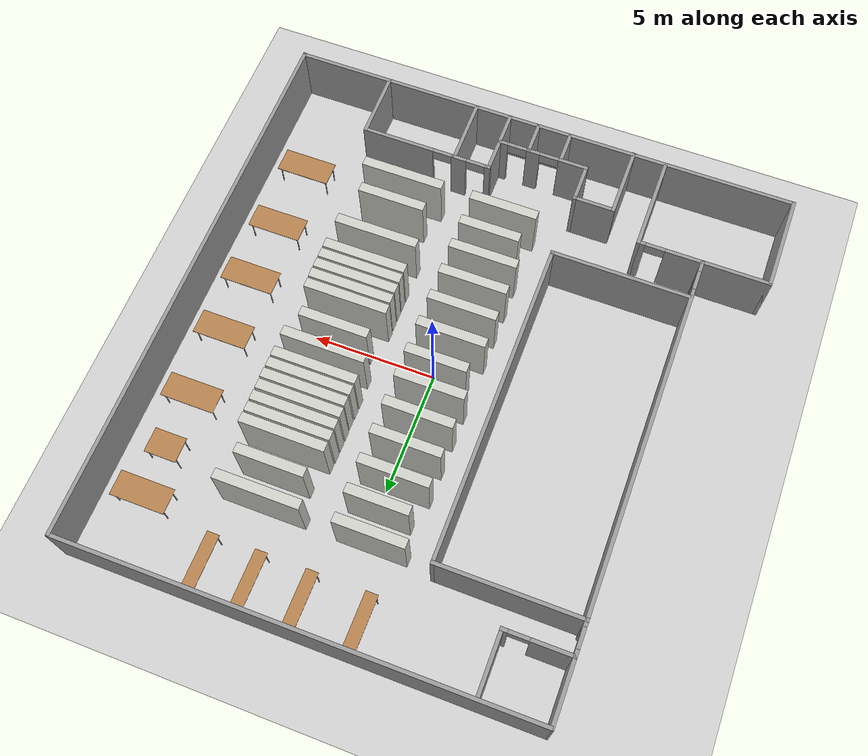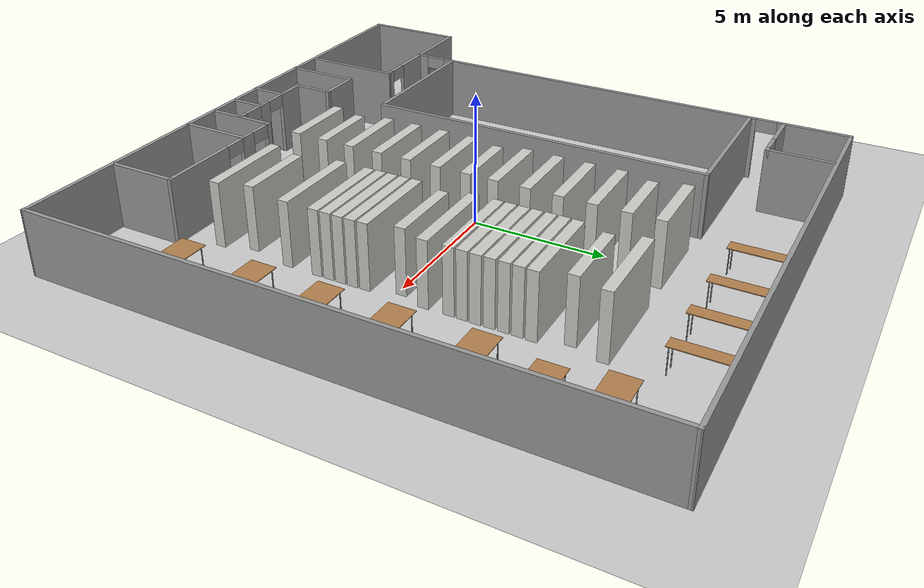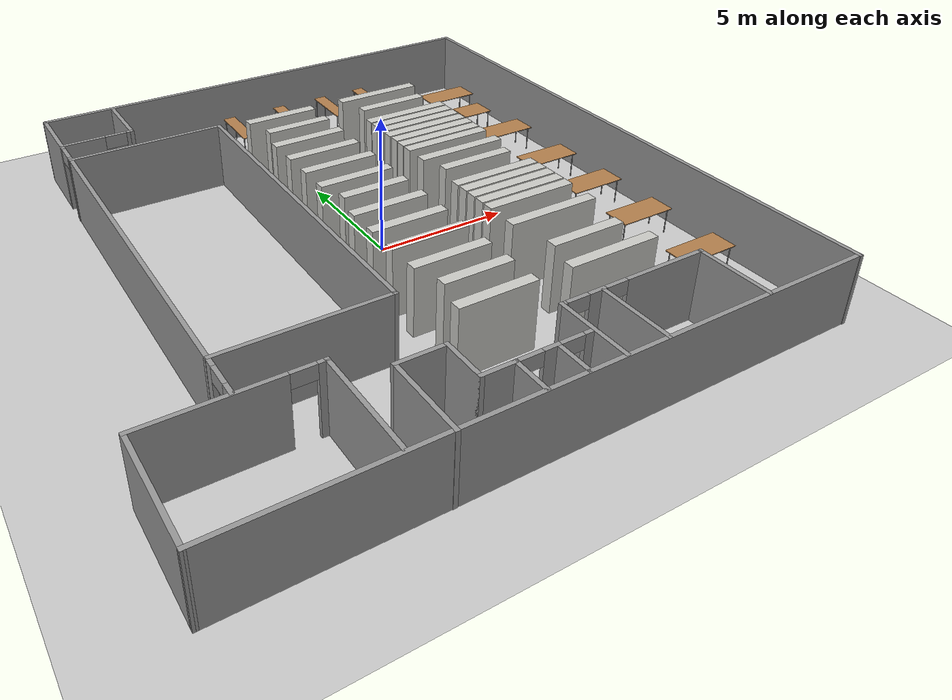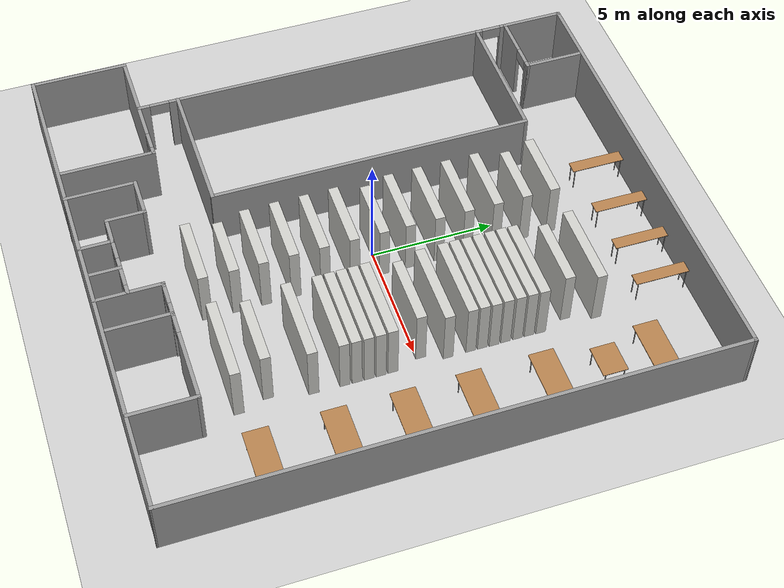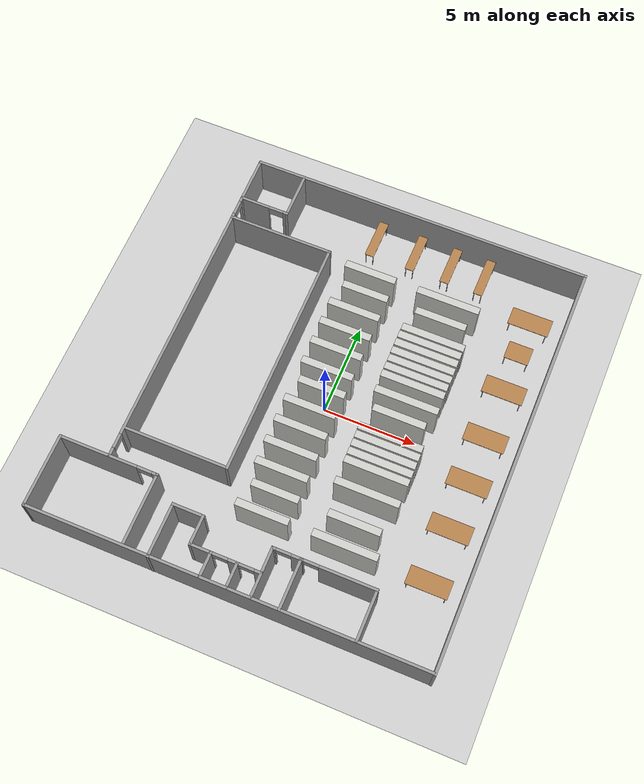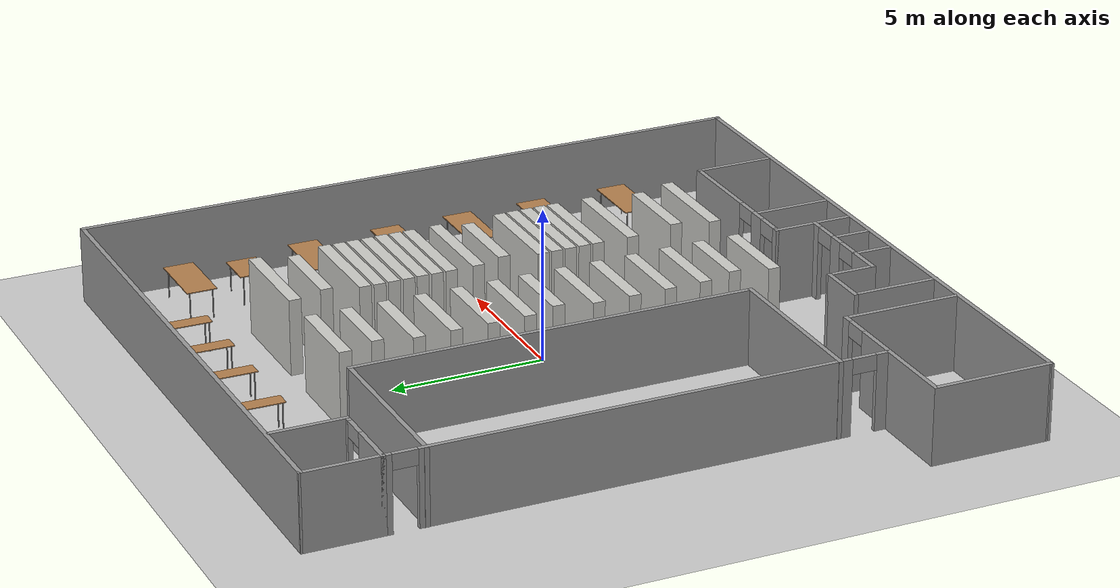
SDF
<sdf version="1.6">
 <world name="default">
  <light name="sun" type="directional">
   <pose>0 0 10 0 -0 0</pose>
   <diffuse>0.8 0.8 0.8 1</diffuse>
   <specular>0.2 0.2 0.2 1</specular>
   <attenuation>
    <range>1000</range>
    <constant>0.9</constant>
    <linear>0.01</linear>
    <quadratic>0.001</quadratic>
   </attenuation>
   <direction>-0.5 0.1 -0.9</direction>
  </light>
  <model name="ground_plane">
   <static>1</static>
   <link name="link">
    <collision name="collision">
     <geometry><plane><normal>0 0 1</normal><size>100 100</size></plane></geometry>
     <surface>
      <contact><collide_bitmask>65535</collide_bitmask></contact>
      <friction><ode><mu>100</mu><mu2>50</mu2></ode></friction>
     </surface>
    </collision>
    <visual name="visual">
     <cast_shadows>0</cast_shadows>
     <geometry><plane><normal>0 0 1</normal><size>100 100</size></plane></geometry>
     <material>
      <script><uri>file://media/materials/scripts/gazebo.material</uri><name>Gazebo/Grey</name></script>
     </material>
    </visual>
   </link>
  </model>
  <gravity>0 0 -9.8</gravity>
  <magnetic_field>6e-06 2.3e-05 -4.2e-05</magnetic_field>
  <atmosphere type="adiabatic"/>
  <physics name="default_physics" default="0" type="ode">
   <max_step_size>0.001</max_step_size>
   <real_time_factor>1</real_time_factor>
   <real_time_update_rate>1000</real_time_update_rate>
  </physics>
  <scene><ambient>0.4 0.4 0.4 1</ambient><background>0.7 0.7 0.7 1</background><shadows>1</shadows></scene>
  <audio><device>default</device></audio>
  <spherical_coordinates>
   <surface_model>EARTH_WGS84</surface_model>
   <latitude_deg>0</latitude_deg>
   <longitude_deg>0</longitude_deg>
   <elevation>0</elevation>
   <heading_deg>0</heading_deg>
  </spherical_coordinates>
  <model name="bi_mi_og">
   <pose>-0.524305 0.076707 0 0 -0 0</pose>
   <link name="Wall_100">
    <collision name="Wall_100_Collision">
     <geometry><box><size>3.4 0.4 2.5</size></box></geometry>
     <pose>0 0 1.25 0 -0 0</pose>
    </collision>
    <visual name="Wall_100_Visual">
     <pose>0 0 1.25 0 -0 0</pose>
     <geometry><box><size>3.4 0.4 2.5</size></box></geometry>
     <material>
      <script><uri>file://media/materials/scripts/gazebo.material</uri><name>Gazebo/CeilingTiled</name></script>
      <ambient>0.435294 0.796078 0.67451 1</ambient>
     </material>
     <meta><layer>0</layer></meta>
    </visual>
    <pose>4.47382 -1.12861 0 0 -0 0</pose>
   </link>
   <link name="Wall_102">
    <collision name="Wall_102_Collision">
     <geometry><box><size>3.4 0.4 2.5</size></box></geometry>
     <pose>0 0 1.25 0 -0 0</pose>
    </collision>
    <visual name="Wall_102_Visual">
     <pose>0 0 1.25 0 -0 0</pose>
     <geometry><box><size>3.4 0.4 2.5</size></box></geometry>
     <material>
      <script><uri>file://media/materials/scripts/gazebo.material</uri><name>Gazebo/CeilingTiled</name></script>
      <ambient>0.435294 0.796078 0.67451 1</ambient>
     </material>
     <meta><layer>0</layer></meta>
    </visual>
    <pose>4.48903 -1.6002 0 0 -0 0</pose>
   </link>
   <link name="Wall_104">
    <collision name="Wall_104_Collision">
     <geometry><box><size>3.4 0.4 2.5</size></box></geometry>
     <pose>0 0 1.25 0 -0 0</pose>
    </collision>
    <visual name="Wall_104_Visual">
     <pose>0 0 1.25 0 -0 0</pose>
     <geometry><box><size>3.4 0.4 2.5</size></box></geometry>
     <material>
      <script><uri>file://media/materials/scripts/gazebo.material</uri><name>Gazebo/CeilingTiled</name></script>
      <ambient>0.435294 0.796078 0.67451 1</ambient>
     </material>
     <meta><layer>0</layer></meta>
    </visual>
    <pose>4.48824 -2.07161 0 0 -0 0</pose>
   </link>
   <link name="Wall_106">
    <collision name="Wall_106_Collision">
     <geometry><box><size>3.4 0.4 2.5</size></box></geometry>
     <pose>0 0 1.25 0 -0 0</pose>
    </collision>
    <visual name="Wall_106_Visual">
     <pose>0 0 1.25 0 -0 0</pose>
     <geometry><box><size>3.4 0.4 2.5</size></box></geometry>
     <material>
      <script><uri>file://media/materials/scripts/gazebo.material</uri><name>Gazebo/CeilingTiled</name></script>
      <ambient>0.435294 0.796078 0.67451 1</ambient>
     </material>
     <meta><layer>0</layer></meta>
    </visual>
    <pose>4.48903 -2.54278 0 0 -0 0</pose>
   </link>
   <link name="Wall_108">
    <collision name="Wall_108_Collision">
     <geometry><box><size>3.4 0.4 2.5</size></box></geometry>
     <pose>0 0 1.25 0 -0 0</pose>
    </collision>
    <visual name="Wall_108_Visual">
     <pose>0 0 1.25 0 -0 0</pose>
     <geometry><box><size>3.4 0.4 2.5</size></box></geometry>
     <material>
      <script><uri>file://media/materials/scripts/gazebo.material</uri><name>Gazebo/CeilingTiled</name></script>
      <ambient>0.435294 0.796078 0.67451 1</ambient>
     </material>
     <meta><layer>0</layer></meta>
    </visual>
    <pose>4.48824 -3.01499 0 0 -0 0</pose>
   </link>
   <link name="Wall_11">
    <collision name="Wall_11_Collision">
     <geometry><box><size>21.3169 0.15 2.5</size></box></geometry>
     <pose>0 0 1.25 0 -0 0</pose>
    </collision>
    <visual name="Wall_11_Visual">
     <pose>0 0 1.25 0 -0 0</pose>
     <geometry><box><size>21.3169 0.15 2.5</size></box></geometry>
     <material>
      <script><uri>file://media/materials/scripts/gazebo.material</uri><name>Gazebo/Grey</name></script>
      <ambient>1 1 1 1</ambient>
     </material>
     <meta><layer>0</layer></meta>
    </visual>
    <pose>-3.3e-05 -11.1726 0 0 -0 0.001286</pose>
   </link>
   <link name="Wall_110">
    <collision name="Wall_110_Collision">
     <geometry><box><size>3.4 0.4 2.5</size></box></geometry>
     <pose>0 0 1.25 0 -0 0</pose>
    </collision>
    <visual name="Wall_110_Visual">
     <pose>0 0 1.25 0 -0 0</pose>
     <geometry><box><size>3.4 0.4 2.5</size></box></geometry>
     <material>
      <script><uri>file://media/materials/scripts/gazebo.material</uri><name>Gazebo/CeilingTiled</name></script>
      <ambient>0.435294 0.796078 0.67451 1</ambient>
     </material>
     <meta><layer>0</layer></meta>
    </visual>
    <pose>4.47361 -4.21578 0 0 -0 0</pose>
   </link>
   <link name="Wall_112">
    <collision name="Wall_112_Collision">
     <geometry><box><size>3.4 0.4 2.5</size></box></geometry>
     <pose>0 0 1.25 0 -0 0</pose>
    </collision>
    <visual name="Wall_112_Visual">
     <pose>0 0 1.25 0 -0 0</pose>
     <geometry><box><size>3.4 0.4 2.5</size></box></geometry>
     <material>
      <script><uri>file://media/materials/scripts/gazebo.material</uri><name>Gazebo/CeilingTiled</name></script>
      <ambient>0.435294 0.796078 0.67451 1</ambient>
     </material>
     <meta><layer>0</layer></meta>
    </visual>
    <pose>4.48555 -7.08842 0 0 -0 0</pose>
   </link>
   <link name="Wall_114">
    <collision name="Wall_114_Collision">
     <geometry><box><size>2.75 0.4 2.5</size></box></geometry>
     <pose>0 0 1.25 0 -0 0</pose>
    </collision>
    <visual name="Wall_114_Visual">
     <pose>0 0 1.25 0 -0 0</pose>
     <geometry><box><size>2.75 0.4 2.5</size></box></geometry>
     <material>
      <script><uri>file://media/materials/scripts/gazebo.material</uri><name>Gazebo/CeilingTiled</name></script>
      <ambient>0.435294 0.796078 0.67451 1</ambient>
     </material>
     <meta><layer>0</layer></meta>
    </visual>
    <pose>4.48252 -5.8822 0 0 -0 0</pose>
   </link>
   <link name="Wall_13">
    <collision name="Wall_13_Collision">
     <geometry><box><size>22.5 0.15 2.5</size></box></geometry>
     <pose>0 0 1.25 0 -0 0</pose>
    </collision>
    <visual name="Wall_13_Visual">
     <pose>0 0 1.25 0 -0 0</pose>
     <geometry><box><size>22.5 0.15 2.5</size></box></geometry>
     <material>
      <script><uri>file://media/materials/scripts/gazebo.material</uri><name>Gazebo/Grey</name></script>
      <ambient>1 1 1 1</ambient>
     </material>
     <meta><layer>0</layer></meta>
    </visual>
    <pose>10.5834 -0.004082 0 0 -0 1.5708</pose>
   </link>
   <link name="Wall_15">
    <collision name="Wall_15_Collision">
     <geometry><box><size>18.6299 0.15 2.5</size></box></geometry>
     <pose>0 0 1.25 0 -0 0</pose>
    </collision>
    <visual name="Wall_15_Visual">
     <pose>0 0 1.25 0 -0 0</pose>
     <geometry><box><size>18.6299 0.15 2.5</size></box></geometry>
     <material>
      <script><uri>file://media/materials/scripts/gazebo.material</uri><name>Gazebo/Grey</name></script>
      <ambient>1 1 1 1</ambient>
     </material>
     <meta><layer>0</layer></meta>
    </visual>
    <pose>1.34347 11.1709 0 0 -0 -3.13942</pose>
   </link>
   <link name="Wall_17">
    <collision name="Wall_17_Collision">
     <geometry><box><size>2.6 0.15 2.5</size></box></geometry>
     <pose>0 0 1.25 0 -0 0</pose>
    </collision>
    <visual name="Wall_17_Visual">
     <pose>0 0 1.25 0 -0 0</pose>
     <geometry><box><size>2.6 0.15 2.5</size></box></geometry>
     <material>
      <script><uri>file://media/materials/scripts/gazebo.material</uri><name>Gazebo/Grey</name></script>
      <ambient>1 1 1 1</ambient>
     </material>
     <meta><layer>0</layer></meta>
    </visual>
    <pose>-7.89648 9.92581 0 0 -0 -1.5708</pose>
   </link>
   <link name="Wall_19">
    <pose>-6.59648 8.70081 0 0 -0 0</pose>
    <visual name="Wall_19_Visual_0">
     <pose>-0.546292 0 1.25 0 -0 0</pose>
     <geometry><box><size>1.65742 0.15 2.5</size></box></geometry>
     <material>
      <script><uri>file://media/materials/scripts/gazebo.material</uri><name>Gazebo/Grey</name></script>
      <ambient>1 1 1 1</ambient>
     </material>
     <meta><layer>0</layer></meta>
    </visual>
    <collision name="Wall_19_Collision_0">
     <geometry><box><size>1.65742 0.15 2.5</size></box></geometry>
     <pose>-0.546292 0 1.25 0 -0 0</pose>
    </collision>
    <visual name="Wall_19_Visual_1">
     <pose>1.22871 0 1.25 0 -0 0</pose>
     <geometry><box><size>0.292584 0.15 2.5</size></box></geometry>
     <material>
      <script><uri>file://media/materials/scripts/gazebo.material</uri><name>Gazebo/Grey</name></script>
      <ambient>1 1 1 1</ambient>
     </material>
     <meta><layer>0</layer></meta>
    </visual>
    <collision name="Wall_19_Collision_1">
     <geometry><box><size>0.292584 0.15 2.5</size></box></geometry>
     <pose>1.22871 0 1.25 0 -0 0</pose>
    </collision>
    <visual name="Wall_19_Visual_2">
     <pose>0.682416 0 2.25 0 -0 0</pose>
     <geometry><box><size>0.8 0.15 0.5</size></box></geometry>
     <material>
      <script><uri>file://media/materials/scripts/gazebo.material</uri><name>Gazebo/Grey</name></script>
      <ambient>1 1 1 1</ambient>
     </material>
     <meta><layer>0</layer></meta>
    </visual>
    <collision name="Wall_19_Collision_2">
     <geometry><box><size>0.8 0.15 0.5</size></box></geometry>
     <pose>0.682416 0 2.25 0 -0 0</pose>
    </collision>
   </link>
   <link name="Wall_20">
    <collision name="Wall_20_Collision">
     <geometry><box><size>2.5 0.15 2.5</size></box></geometry>
     <pose>0 0 1.25 0 -0 0</pose>
    </collision>
    <visual name="Wall_20_Visual">
     <pose>0 0 1.25 0 -0 0</pose>
     <geometry><box><size>2.5 0.15 2.5</size></box></geometry>
     <material>
      <script><uri>file://media/materials/scripts/gazebo.material</uri><name>Gazebo/Grey</name></script>
      <ambient>1 1 1 1</ambient>
     </material>
     <meta><layer>0</layer></meta>
    </visual>
    <pose>-5.29648 9.8758 0 0 -0 1.5708</pose>
   </link>
   <link name="Wall_22">
    <pose>-7.89648 0.700805 0 0 -0 -1.5708</pose>
    <visual name="Wall_22_Visual_0">
     <pose>-7.90982 0 1.25 0 -0 0</pose>
     <geometry><box><size>0.330356 0.15 2.5</size></box></geometry>
     <material>
      <script><uri>file://media/materials/scripts/gazebo.material</uri><name>Gazebo/Grey</name></script>
      <ambient>1 1 1 1</ambient>
     </material>
     <meta><layer>0</layer></meta>
    </visual>
    <collision name="Wall_22_Collision_0">
     <geometry><box><size>0.330356 0.15 2.5</size></box></geometry>
     <pose>-7.90982 0 1.25 0 -0 0</pose>
    </collision>
    <visual name="Wall_22_Visual_1">
     <pose>-0.08023 0 1.25 0 -0 0</pose>
     <geometry><box><size>13.7288 0.15 2.5</size></box></geometry>
     <material>
      <script><uri>file://media/materials/scripts/gazebo.material</uri><name>Gazebo/Grey</name></script>
      <ambient>1 1 1 1</ambient>
     </material>
     <meta><layer>0</layer></meta>
    </visual>
    <collision name="Wall_22_Collision_1">
     <geometry><box><size>13.7288 0.15 2.5</size></box></geometry>
     <pose>-0.08023 0 1.25 0 -0 0</pose>
    </collision>
    <visual name="Wall_22_Visual_2">
     <pose>7.82959 0 1.25 0 -0 0</pose>
     <geometry><box><size>0.490815 0.15 2.5</size></box></geometry>
     <material>
      <script><uri>file://media/materials/scripts/gazebo.material</uri><name>Gazebo/Grey</name></script>
      <ambient>1 1 1 1</ambient>
     </material>
     <meta><layer>0</layer></meta>
    </visual>
    <collision name="Wall_22_Collision_2">
     <geometry><box><size>0.490815 0.15 2.5</size></box></geometry>
     <pose>7.82959 0 1.25 0 -0 0</pose>
    </collision>
    <visual name="Wall_22_Visual_3">
     <pose>-7.34464 0 2.25 0 -0 0</pose>
     <geometry><box><size>0.8 0.15 0.5</size></box></geometry>
     <material>
      <script><uri>file://media/materials/scripts/gazebo.material</uri><name>Gazebo/Grey</name></script>
      <ambient>1 1 1 1</ambient>
     </material>
     <meta><layer>0</layer></meta>
    </visual>
    <collision name="Wall_22_Collision_3">
     <geometry><box><size>0.8 0.15 0.5</size></box></geometry>
     <pose>-7.34464 0 2.25 0 -0 0</pose>
    </collision>
    <visual name="Wall_22_Visual_4">
     <pose>7.18419 0 2.25 0 -0 0</pose>
     <geometry><box><size>0.8 0.15 0.5</size></box></geometry>
     <material>
      <script><uri>file://media/materials/scripts/gazebo.material</uri><name>Gazebo/Grey</name></script>
      <ambient>1 1 1 1</ambient>
     </material>
     <meta><layer>0</layer></meta>
    </visual>
    <collision name="Wall_22_Collision_4">
     <geometry><box><size>0.8 0.15 0.5</size></box></geometry>
     <pose>7.18419 0 2.25 0 -0 0</pose>
    </collision>
   </link>
   <link name="Wall_24">
    <collision name="Wall_24_Collision">
     <geometry><box><size>4 0.15 2.5</size></box></geometry>
     <pose>0 0 1.25 0 -0 0</pose>
    </collision>
    <visual name="Wall_24_Visual">
     <pose>0 0 1.25 0 -0 0</pose>
     <geometry><box><size>4 0.15 2.5</size></box></geometry>
     <material>
      <script><uri>file://media/materials/scripts/gazebo.material</uri><name>Gazebo/Grey</name></script>
      <ambient>1 1 1 1</ambient>
     </material>
     <meta><layer>0</layer></meta>
    </visual>
    <pose>-10.5835 -9.2612 0 0 -0 1.5708</pose>
   </link>
   <link name="Wall_26">
    <pose>-7.94498 -7.3362 0 0 -0 0</pose>
    <visual name="Wall_26_Visual_0">
     <pose>-0.579795 0 1.25 0 -0 0</pose>
     <geometry><box><size>4.26728 0.15 2.5</size></box></geometry>
     <material>
      <script><uri>file://media/materials/scripts/gazebo.material</uri><name>Gazebo/Grey</name></script>
      <ambient>1 1 1 1</ambient>
     </material>
     <meta><layer>0</layer></meta>
    </visual>
    <collision name="Wall_26_Collision_0">
     <geometry><box><size>4.26728 0.15 2.5</size></box></geometry>
     <pose>-0.579795 0 1.25 0 -0 0</pose>
    </collision>
    <visual name="Wall_26_Visual_1">
     <pose>2.53364 0 1.25 0 -0 0</pose>
     <geometry><box><size>0.359591 0.15 2.5</size></box></geometry>
     <material>
      <script><uri>file://media/materials/scripts/gazebo.material</uri><name>Gazebo/Grey</name></script>
      <ambient>1 1 1 1</ambient>
     </material>
     <meta><layer>0</layer></meta>
    </visual>
    <collision name="Wall_26_Collision_1">
     <geometry><box><size>0.359591 0.15 2.5</size></box></geometry>
     <pose>2.53364 0 1.25 0 -0 0</pose>
    </collision>
    <visual name="Wall_26_Visual_2">
     <pose>1.95384 0 2.25 0 -0 0</pose>
     <geometry><box><size>0.8 0.15 0.5</size></box></geometry>
     <material>
      <script><uri>file://media/materials/scripts/gazebo.material</uri><name>Gazebo/Grey</name></script>
      <ambient>1 1 1 1</ambient>
     </material>
     <meta><layer>0</layer></meta>
    </visual>
    <collision name="Wall_26_Collision_2">
     <geometry><box><size>0.8 0.15 0.5</size></box></geometry>
     <pose>1.95384 0 2.25 0 -0 0</pose>
    </collision>
   </link>
   <link name="Wall_28">
    <collision name="Wall_28_Collision">
     <geometry><box><size>3.9 0.15 2.5</size></box></geometry>
     <pose>0 0 1.25 0 -0 0</pose>
    </collision>
    <visual name="Wall_28_Visual">
     <pose>0 0 1.25 0 -0 0</pose>
     <geometry><box><size>3.9 0.15 2.5</size></box></geometry>
     <material>
      <script><uri>file://media/materials/scripts/gazebo.material</uri><name>Gazebo/Grey</name></script>
      <ambient>1 1 1 1</ambient>
     </material>
     <meta><layer>0</layer></meta>
    </visual>
    <pose>-5.30648 -9.2112 0 0 -0 -1.5708</pose>
   </link>
   <link name="Wall_30">
    <collision name="Wall_30_Collision">
     <geometry><box><size>5.75 0.15 2.5</size></box></geometry>
     <pose>0 0 1.25 0 -0 0</pose>
    </collision>
    <visual name="Wall_30_Visual">
     <pose>0 0 1.25 0 -0 0</pose>
     <geometry><box><size>5.75 0.15 2.5</size></box></geometry>
     <material>
      <script><uri>file://media/materials/scripts/gazebo.material</uri><name>Gazebo/Grey</name></script>
      <ambient>1 1 1 1</ambient>
     </material>
     <meta><layer>0</layer></meta>
    </visual>
    <pose>-5.10418 -5.69691 0 0 -0 0</pose>
   </link>
   <link name="Wall_31">
    <collision name="Wall_31_Collision">
     <geometry><box><size>13.25 0.15 2.5</size></box></geometry>
     <pose>0 0 1.25 0 -0 0</pose>
    </collision>
    <visual name="Wall_31_Visual">
     <pose>0 0 1.25 0 -0 0</pose>
     <geometry><box><size>13.25 0.15 2.5</size></box></geometry>
     <material>
      <script><uri>file://media/materials/scripts/gazebo.material</uri><name>Gazebo/Grey</name></script>
      <ambient>1 1 1 1</ambient>
     </material>
     <meta><layer>0</layer></meta>
    </visual>
    <pose>-2.30418 0.853088 0 0 -0 1.5708</pose>
   </link>
   <link name="Wall_32">
    <collision name="Wall_32_Collision">
     <geometry><box><size>5.75 0.15 2.5</size></box></geometry>
     <pose>0 0 1.25 0 -0 0</pose>
    </collision>
    <visual name="Wall_32_Visual">
     <pose>0 0 1.25 0 -0 0</pose>
     <geometry><box><size>5.75 0.15 2.5</size></box></geometry>
     <material>
      <script><uri>file://media/materials/scripts/gazebo.material</uri><name>Gazebo/Grey</name></script>
      <ambient>1 1 1 1</ambient>
     </material>
     <meta><layer>0</layer></meta>
    </visual>
    <pose>-5.10418 7.40309 0 0 -0 3.14159</pose>
   </link>
   <link name="Wall_34">
    <collision name="Wall_34_Collision">
     <geometry><box><size>2.75 0.15 2.5</size></box></geometry>
     <pose>0 0 1.25 0 -0 0</pose>
    </collision>
    <visual name="Wall_34_Visual">
     <pose>0 0 1.25 0 -0 0</pose>
     <geometry><box><size>2.75 0.15 2.5</size></box></geometry>
     <material>
      <script><uri>file://media/materials/scripts/gazebo.material</uri><name>Gazebo/Grey</name></script>
      <ambient>1 1 1 1</ambient>
     </material>
     <meta><layer>0</layer></meta>
    </visual>
    <pose>6.70073 -9.83844 0 0 -0 1.5708</pose>
   </link>
   <link name="Wall_35">
    <pose>4.02573 -8.53843 0 0 -0 3.14159</pose>
    <visual name="Wall_35_Visual_0">
     <pose>-1.23302 0 1.25 0 -0 0</pose>
     <geometry><box><size>3.03397 0.15 2.5</size></box></geometry>
     <material>
      <script><uri>file://media/materials/scripts/gazebo.material</uri><name>Gazebo/Grey</name></script>
      <ambient>1 1 1 1</ambient>
     </material>
     <meta><layer>0</layer></meta>
    </visual>
    <collision name="Wall_35_Collision_0">
     <geometry><box><size>3.03397 0.15 2.5</size></box></geometry>
     <pose>-1.23302 0 1.25 0 -0 0</pose>
    </collision>
    <visual name="Wall_35_Visual_1">
     <pose>1.39809 0 1.25 0 -0 0</pose>
     <geometry><box><size>0.62824 0.15 2.5</size></box></geometry>
     <material>
      <script><uri>file://media/materials/scripts/gazebo.material</uri><name>Gazebo/Grey</name></script>
      <ambient>1 1 1 1</ambient>
     </material>
     <meta><layer>0</layer></meta>
    </visual>
    <collision name="Wall_35_Collision_1">
     <geometry><box><size>0.62824 0.15 2.5</size></box></geometry>
     <pose>1.39809 0 1.25 0 -0 0</pose>
    </collision>
    <visual name="Wall_35_Visual_2">
     <pose>2.6311 0 1.25 0 -0 0</pose>
     <geometry><box><size>0.237794 0.15 2.5</size></box></geometry>
     <material>
      <script><uri>file://media/materials/scripts/gazebo.material</uri><name>Gazebo/Grey</name></script>
      <ambient>1 1 1 1</ambient>
     </material>
     <meta><layer>0</layer></meta>
    </visual>
    <collision name="Wall_35_Collision_2">
     <geometry><box><size>0.237794 0.15 2.5</size></box></geometry>
     <pose>2.6311 0 1.25 0 -0 0</pose>
    </collision>
    <visual name="Wall_35_Visual_3">
     <pose>0.683966 0 2.25 0 -0 0</pose>
     <geometry><box><size>0.8 0.15 0.5</size></box></geometry>
     <material>
      <script><uri>file://media/materials/scripts/gazebo.material</uri><name>Gazebo/Grey</name></script>
      <ambient>1 1 1 1</ambient>
     </material>
     <meta><layer>0</layer></meta>
    </visual>
    <collision name="Wall_35_Collision_3">
     <geometry><box><size>0.8 0.15 0.5</size></box></geometry>
     <pose>0.683966 0 2.25 0 -0 0</pose>
    </collision>
    <visual name="Wall_35_Visual_4">
     <pose>2.11221 0 2.25 0 -0 0</pose>
     <geometry><box><size>0.8 0.15 0.5</size></box></geometry>
     <material>
      <script><uri>file://media/materials/scripts/gazebo.material</uri><name>Gazebo/Grey</name></script>
      <ambient>1 1 1 1</ambient>
     </material>
     <meta><layer>0</layer></meta>
    </visual>
    <collision name="Wall_35_Collision_4">
     <geometry><box><size>0.8 0.15 0.5</size></box></geometry>
     <pose>2.11221 0 2.25 0 -0 0</pose>
    </collision>
   </link>
   <link name="Wall_36">
    <collision name="Wall_36_Collision">
     <geometry><box><size>2.75 0.15 2.5</size></box></geometry>
     <pose>0 0 1.25 0 -0 0</pose>
    </collision>
    <visual name="Wall_36_Visual">
     <pose>0 0 1.25 0 -0 0</pose>
     <geometry><box><size>2.75 0.15 2.5</size></box></geometry>
     <material>
      <script><uri>file://media/materials/scripts/gazebo.material</uri><name>Gazebo/Grey</name></script>
      <ambient>1 1 1 1</ambient>
     </material>
     <meta><layer>0</layer></meta>
    </visual>
    <pose>1.35073 -9.83844 0 0 -0 -1.5708</pose>
   </link>
   <link name="Wall_38">
    <collision name="Wall_38_Collision">
     <geometry><box><size>2.75 0.15 2.5</size></box></geometry>
     <pose>0 0 1.25 0 -0 0</pose>
    </collision>
    <visual name="Wall_38_Visual">
     <pose>0 0 1.25 0 -0 0</pose>
     <geometry><box><size>2.75 0.15 2.5</size></box></geometry>
     <material>
      <script><uri>file://media/materials/scripts/gazebo.material</uri><name>Gazebo/Grey</name></script>
      <ambient>1 1 1 1</ambient>
     </material>
     <meta><layer>0</layer></meta>
    </visual>
    <pose>2.81881 -9.8639 0 0 -0 -1.5708</pose>
   </link>
   <link name="Wall_40">
    <pose>-0.499477 -9.89119 0 0 -0 3.14159</pose>
    <visual name="Wall_40_Visual_0">
     <pose>-1.70534 0 1.25 0 -0 0</pose>
     <geometry><box><size>0.43932 0.15 2.5</size></box></geometry>
     <material>
      <script><uri>file://media/materials/scripts/gazebo.material</uri><name>Gazebo/Grey</name></script>
      <ambient>1 1 1 1</ambient>
     </material>
     <meta><layer>0</layer></meta>
    </visual>
    <collision name="Wall_40_Collision_0">
     <geometry><box><size>0.43932 0.15 2.5</size></box></geometry>
     <pose>-1.70534 0 1.25 0 -0 0</pose>
    </collision>
    <visual name="Wall_40_Visual_1">
     <pose>-0.401819 0 1.25 0 -0 0</pose>
     <geometry><box><size>0.567723 0.15 2.5</size></box></geometry>
     <material>
      <script><uri>file://media/materials/scripts/gazebo.material</uri><name>Gazebo/Grey</name></script>
      <ambient>1 1 1 1</ambient>
     </material>
     <meta><layer>0</layer></meta>
    </visual>
    <collision name="Wall_40_Collision_1">
     <geometry><box><size>0.567723 0.15 2.5</size></box></geometry>
     <pose>-0.401819 0 1.25 0 -0 0</pose>
    </collision>
    <visual name="Wall_40_Visual_2">
     <pose>1.30352 0 1.25 0 -0 0</pose>
     <geometry><box><size>1.24296 0.15 2.5</size></box></geometry>
     <material>
      <script><uri>file://media/materials/scripts/gazebo.material</uri><name>Gazebo/Grey</name></script>
      <ambient>1 1 1 1</ambient>
     </material>
     <meta><layer>0</layer></meta>
    </visual>
    <collision name="Wall_40_Collision_2">
     <geometry><box><size>1.24296 0.15 2.5</size></box></geometry>
     <pose>1.30352 0 1.25 0 -0 0</pose>
    </collision>
    <visual name="Wall_40_Visual_3">
     <pose>-1.08568 0 2.25 0 -0 0</pose>
     <geometry><box><size>0.8 0.15 0.5</size></box></geometry>
     <material>
      <script><uri>file://media/materials/scripts/gazebo.material</uri><name>Gazebo/Grey</name></script>
      <ambient>1 1 1 1</ambient>
     </material>
     <meta><layer>0</layer></meta>
    </visual>
    <collision name="Wall_40_Collision_3">
     <geometry><box><size>0.8 0.15 0.5</size></box></geometry>
     <pose>-1.08568 0 2.25 0 -0 0</pose>
    </collision>
    <visual name="Wall_40_Visual_4">
     <pose>0.282043 0 2.25 0 -0 0</pose>
     <geometry><box><size>0.8 0.15 0.5</size></box></geometry>
     <material>
      <script><uri>file://media/materials/scripts/gazebo.material</uri><name>Gazebo/Grey</name></script>
      <ambient>1 1 1 1</ambient>
     </material>
     <meta><layer>0</layer></meta>
    </visual>
    <collision name="Wall_40_Collision_4">
     <geometry><box><size>0.8 0.15 0.5</size></box></geometry>
     <pose>0.282043 0 2.25 0 -0 0</pose>
    </collision>
   </link>
   <link name="Wall_42">
    <collision name="Wall_42_Collision">
     <geometry><box><size>1.65 0.15 2.5</size></box></geometry>
     <pose>0 0 1.25 0 -0 0</pose>
    </collision>
    <visual name="Wall_42_Visual">
     <pose>0 0 1.25 0 -0 0</pose>
     <geometry><box><size>1.65 0.15 2.5</size></box></geometry>
     <material>
      <script><uri>file://media/materials/scripts/gazebo.material</uri><name>Gazebo/Grey</name></script>
      <ambient>1 1 1 1</ambient>
     </material>
     <meta><layer>0</layer></meta>
    </visual>
    <pose>-2.34948 -9.14119 0 0 -0 1.5708</pose>
   </link>
   <link name="Wall_44">
    <collision name="Wall_44_Collision">
     <geometry><box><size>1.75 0.15 2.5</size></box></geometry>
     <pose>0 0 1.25 0 -0 0</pose>
    </collision>
    <visual name="Wall_44_Visual">
     <pose>0 0 1.25 0 -0 0</pose>
     <geometry><box><size>1.75 0.15 2.5</size></box></geometry>
     <material>
      <script><uri>file://media/materials/scripts/gazebo.material</uri><name>Gazebo/Grey</name></script>
      <ambient>1 1 1 1</ambient>
     </material>
     <meta><layer>0</layer></meta>
    </visual>
    <pose>-3.14948 -8.39119 0 0 -0 3.14159</pose>
   </link>
   <link name="Wall_45">
    <collision name="Wall_45_Collision">
     <geometry><box><size>2.95 0.15 2.5</size></box></geometry>
     <pose>0 0 1.25 0 -0 0</pose>
    </collision>
    <visual name="Wall_45_Visual">
     <pose>0 0 1.25 0 -0 0</pose>
     <geometry><box><size>2.95 0.15 2.5</size></box></geometry>
     <material>
      <script><uri>file://media/materials/scripts/gazebo.material</uri><name>Gazebo/Grey</name></script>
      <ambient>1 1 1 1</ambient>
     </material>
     <meta><layer>0</layer></meta>
    </visual>
    <pose>-3.94948 -9.7912 0 0 -0 -1.5708</pose>
   </link>
   <link name="Wall_47">
    <collision name="Wall_47_Collision">
     <geometry><box><size>1.4 0.15 2.5</size></box></geometry>
     <pose>0 0 1.25 0 -0 0</pose>
    </collision>
    <visual name="Wall_47_Visual">
     <pose>0 0 1.25 0 -0 0</pose>
     <geometry><box><size>1.4 0.15 2.5</size></box></geometry>
     <material>
      <script><uri>file://media/materials/scripts/gazebo.material</uri><name>Gazebo/Grey</name></script>
      <ambient>1 1 1 1</ambient>
     </material>
     <meta><layer>0</layer></meta>
    </visual>
    <pose>-1.26448 -10.5162 0 0 -0 -1.5708</pose>
   </link>
   <link name="Wall_49">
    <collision name="Wall_49_Collision">
     <geometry><box><size>1.4 0.15 2.5</size></box></geometry>
     <pose>0 0 1.25 0 -0 0</pose>
    </collision>
    <visual name="Wall_49_Visual">
     <pose>0 0 1.25 0 -0 0</pose>
     <geometry><box><size>1.4 0.15 2.5</size></box></geometry>
     <material>
      <script><uri>file://media/materials/scripts/gazebo.material</uri><name>Gazebo/Grey</name></script>
      <ambient>1 1 1 1</ambient>
     </material>
     <meta><layer>0</layer></meta>
    </visual>
    <pose>0.103523 -10.5162 0 0 -0 -1.5708</pose>
   </link>
   <link name="Wall_51">
    <collision name="Wall_51_Collision">
     <geometry><box><size>2.8 0.4 2.5</size></box></geometry>
     <pose>0 0 1.25 0 -0 0</pose>
    </collision>
    <visual name="Wall_51_Visual">
     <pose>0 0 1.25 0 -0 0</pose>
     <geometry><box><size>2.8 0.4 2.5</size></box></geometry>
     <material>
      <script><uri>file://media/materials/scripts/gazebo.material</uri><name>Gazebo/CeilingTiled</name></script>
      <ambient>0.435294 0.796078 0.67451 1</ambient>
     </material>
     <meta><layer>0</layer></meta>
    </visual>
    <pose>0.173523 -7.08307 0 0 -0 0</pose>
   </link>
   <link name="Wall_53">
    <collision name="Wall_53_Collision">
     <geometry><box><size>2.5 0.4 2.5</size></box></geometry>
     <pose>0 0 1.25 0 -0 0</pose>
    </collision>
    <visual name="Wall_53_Visual">
     <pose>0 0 1.25 0 -0 0</pose>
     <geometry><box><size>2.5 0.4 2.5</size></box></geometry>
     <material>
      <script><uri>file://media/materials/scripts/gazebo.material</uri><name>Gazebo/CeilingTiled</name></script>
      <ambient>0.435294 0.796078 0.67451 1</ambient>
     </material>
     <meta><layer>0</layer></meta>
    </visual>
    <pose>0.341315 -5.87999 0 0 -0 0</pose>
   </link>
   <link name="Wall_55">
    <collision name="Wall_55_Collision">
     <geometry><box><size>2.8 0.4 2.5</size></box></geometry>
     <pose>0 0 1.25 0 -0 0</pose>
    </collision>
    <visual name="Wall_55_Visual">
     <pose>0 0 1.25 0 -0 0</pose>
     <geometry><box><size>2.8 0.4 2.5</size></box></geometry>
     <material>
      <script><uri>file://media/materials/scripts/gazebo.material</uri><name>Gazebo/CeilingTiled</name></script>
      <ambient>0.435294 0.796078 0.67451 1</ambient>
     </material>
     <meta><layer>0</layer></meta>
    </visual>
    <pose>0.185205 -4.72831 0 0 -0 0</pose>
   </link>
   <link name="Wall_57">
    <collision name="Wall_57_Collision">
     <geometry><box><size>2.8 0.4 2.5</size></box></geometry>
     <pose>0 0 1.25 0 -0 0</pose>
    </collision>
    <visual name="Wall_57_Visual">
     <pose>0 0 1.25 0 -0 0</pose>
     <geometry><box><size>2.8 0.4 2.5</size></box></geometry>
     <material>
      <script><uri>file://media/materials/scripts/gazebo.material</uri><name>Gazebo/CeilingTiled</name></script>
      <ambient>0.435294 0.796078 0.67451 1</ambient>
     </material>
     <meta><layer>0</layer></meta>
    </visual>
    <pose>0.167046 -3.52746 0 0 -0 0</pose>
   </link>
   <link name="Wall_60">
    <collision name="Wall_60_Collision">
     <geometry><box><size>2.8 0.4 2.5</size></box></geometry>
     <pose>0 0 1.25 0 -0 0</pose>
    </collision>
    <visual name="Wall_60_Visual">
     <pose>0 0 1.25 0 -0 0</pose>
     <geometry><box><size>2.8 0.4 2.5</size></box></geometry>
     <material>
      <script><uri>file://media/materials/scripts/gazebo.material</uri><name>Gazebo/CeilingTiled</name></script>
      <ambient>0.435294 0.796078 0.67451 1</ambient>
     </material>
     <meta><layer>0</layer></meta>
    </visual>
    <pose>0.166915 -2.32446 0 0 -0 0</pose>
   </link>
   <link name="Wall_62">
    <collision name="Wall_62_Collision">
     <geometry><box><size>2.8 0.4 2.5</size></box></geometry>
     <pose>0 0 1.25 0 -0 0</pose>
    </collision>
    <visual name="Wall_62_Visual">
     <pose>0 0 1.25 0 -0 0</pose>
     <geometry><box><size>2.8 0.4 2.5</size></box></geometry>
     <material>
      <script><uri>file://media/materials/scripts/gazebo.material</uri><name>Gazebo/CeilingTiled</name></script>
      <ambient>0.435294 0.796078 0.67451 1</ambient>
     </material>
     <meta><layer>0</layer></meta>
    </visual>
    <pose>0.167307 -1.12146 0 0 -0 0</pose>
   </link>
   <link name="Wall_64">
    <collision name="Wall_64_Collision">
     <geometry><box><size>2.5 0.4 2.5</size></box></geometry>
     <pose>0 0 1.25 0 -0 0</pose>
    </collision>
    <visual name="Wall_64_Visual">
     <pose>0 0 1.25 0 -0 0</pose>
     <geometry><box><size>2.5 0.4 2.5</size></box></geometry>
     <material>
      <script><uri>file://media/materials/scripts/gazebo.material</uri><name>Gazebo/CeilingTiled</name></script>
      <ambient>0.435294 0.796078 0.67451 1</ambient>
     </material>
     <meta><layer>0</layer></meta>
    </visual>
    <pose>0.318523 0.081805 0 0 -0 0</pose>
   </link>
   <link name="Wall_66">
    <collision name="Wall_66_Collision">
     <geometry><box><size>2.8 0.4 2.5</size></box></geometry>
     <pose>0 0 1.25 0 -0 0</pose>
    </collision>
    <visual name="Wall_66_Visual">
     <pose>0 0 1.25 0 -0 0</pose>
     <geometry><box><size>2.8 0.4 2.5</size></box></geometry>
     <material>
      <script><uri>file://media/materials/scripts/gazebo.material</uri><name>Gazebo/CeilingTiled</name></script>
      <ambient>0.435294 0.796078 0.67451 1</ambient>
     </material>
     <meta><layer>0</layer></meta>
    </visual>
    <pose>0.167046 1.14222 0 0 -0 0</pose>
   </link>
   <link name="Wall_68">
    <collision name="Wall_68_Collision">
     <geometry><box><size>2.8 0.4 2.5</size></box></geometry>
     <pose>0 0 1.25 0 -0 0</pose>
    </collision>
    <visual name="Wall_68_Visual">
     <pose>0 0 1.25 0 -0 0</pose>
     <geometry><box><size>2.8 0.4 2.5</size></box></geometry>
     <material>
      <script><uri>file://media/materials/scripts/gazebo.material</uri><name>Gazebo/CeilingTiled</name></script>
      <ambient>0.435294 0.796078 0.67451 1</ambient>
     </material>
     <meta><layer>0</layer></meta>
    </visual>
    <pose>0.167176 2.34767 0 0 -0 0</pose>
   </link>
   <link name="Wall_70">
    <collision name="Wall_70_Collision">
     <geometry><box><size>2.8 0.4 2.5</size></box></geometry>
     <pose>0 0 1.25 0 -0 0</pose>
    </collision>
    <visual name="Wall_70_Visual">
     <pose>0 0 1.25 0 -0 0</pose>
     <geometry><box><size>2.8 0.4 2.5</size></box></geometry>
     <material>
      <script><uri>file://media/materials/scripts/gazebo.material</uri><name>Gazebo/CeilingTiled</name></script>
      <ambient>0.435294 0.796078 0.67451 1</ambient>
     </material>
     <meta><layer>0</layer></meta>
    </visual>
    <pose>0.167307 3.5508 0 0 -0 0</pose>
   </link>
   <link name="Wall_72">
    <collision name="Wall_72_Collision">
     <geometry><box><size>2.8 0.4 2.5</size></box></geometry>
     <pose>0 0 1.25 0 -0 0</pose>
    </collision>
    <visual name="Wall_72_Visual">
     <pose>0 0 1.25 0 -0 0</pose>
     <geometry><box><size>2.8 0.4 2.5</size></box></geometry>
     <material>
      <script><uri>file://media/materials/scripts/gazebo.material</uri><name>Gazebo/CeilingTiled</name></script>
      <ambient>0.435294 0.796078 0.67451 1</ambient>
     </material>
     <meta><layer>0</layer></meta>
    </visual>
    <pose>0.166699 4.7538 0 0 -0 0</pose>
   </link>
   <link name="Wall_74">
    <collision name="Wall_74_Collision">
     <geometry><box><size>2.5 0.4 2.5</size></box></geometry>
     <pose>0 0 1.25 0 -0 0</pose>
    </collision>
    <visual name="Wall_74_Visual">
     <pose>0 0 1.25 0 -0 0</pose>
     <geometry><box><size>2.5 0.4 2.5</size></box></geometry>
     <material>
      <script><uri>file://media/materials/scripts/gazebo.material</uri><name>Gazebo/CeilingTiled</name></script>
      <ambient>0.435294 0.796078 0.67451 1</ambient>
     </material>
     <meta><layer>0</layer></meta>
    </visual>
    <pose>0.317307 5.95654 0 0 -0 0</pose>
   </link>
   <link name="Wall_76">
    <collision name="Wall_76_Collision">
     <geometry><box><size>2.8 0.4 2.5</size></box></geometry>
     <pose>0 0 1.25 0 -0 0</pose>
    </collision>
    <visual name="Wall_76_Visual">
     <pose>0 0 1.25 0 -0 0</pose>
     <geometry><box><size>2.8 0.4 2.5</size></box></geometry>
     <material>
      <script><uri>file://media/materials/scripts/gazebo.material</uri><name>Gazebo/CeilingTiled</name></script>
      <ambient>0.435294 0.796078 0.67451 1</ambient>
     </material>
     <meta><layer>0</layer></meta>
    </visual>
    <pose>0.149482 7.11254 0 0 -0 3.14159</pose>
   </link>
   <link name="Wall_78">
    <collision name="Wall_78_Collision">
     <geometry><box><size>3.4 0.4 2.5</size></box></geometry>
     <pose>0 0 1.25 0 -0 0</pose>
    </collision>
    <visual name="Wall_78_Visual">
     <pose>0 0 1.25 0 -0 0</pose>
     <geometry><box><size>3.4 0.4 2.5</size></box></geometry>
     <material>
      <script><uri>file://media/materials/scripts/gazebo.material</uri><name>Gazebo/CeilingTiled</name></script>
      <ambient>0.435294 0.796078 0.67451 1</ambient>
     </material>
     <meta><layer>0</layer></meta>
    </visual>
    <pose>4.47357 7.1146 0 0 -0 0</pose>
   </link>
   <link name="Wall_80">
    <collision name="Wall_80_Collision">
     <geometry><box><size>2.75 0.4 2.5</size></box></geometry>
     <pose>0 0 1.25 0 -0 0</pose>
    </collision>
    <visual name="Wall_80_Visual">
     <pose>0 0 1.25 0 -0 0</pose>
     <geometry><box><size>2.75 0.4 2.5</size></box></geometry>
     <material>
      <script><uri>file://media/materials/scripts/gazebo.material</uri><name>Gazebo/CeilingTiled</name></script>
      <ambient>0.435294 0.796078 0.67451 1</ambient>
     </material>
     <meta><layer>0</layer></meta>
    </visual>
    <pose>4.48352 5.95901 0 0 -0 0</pose>
   </link>
   <link name="Wall_82">
    <collision name="Wall_82_Collision">
     <geometry><box><size>3.4 0.4 2.5</size></box></geometry>
     <pose>0 0 1.25 0 -0 0</pose>
    </collision>
    <visual name="Wall_82_Visual">
     <pose>0 0 1.25 0 -0 0</pose>
     <geometry><box><size>3.4 0.4 2.5</size></box></geometry>
     <material>
      <script><uri>file://media/materials/scripts/gazebo.material</uri><name>Gazebo/CeilingTiled</name></script>
      <ambient>0.435294 0.796078 0.67451 1</ambient>
     </material>
     <meta><layer>0</layer></meta>
    </visual>
    <pose>4.48824 4.81801 0 0 -0 0</pose>
   </link>
   <link name="Wall_84">
    <collision name="Wall_84_Collision">
     <geometry><box><size>3.4 0.4 2.5</size></box></geometry>
     <pose>0 0 1.25 0 -0 0</pose>
    </collision>
    <visual name="Wall_84_Visual">
     <pose>0 0 1.25 0 -0 0</pose>
     <geometry><box><size>3.4 0.4 2.5</size></box></geometry>
     <material>
      <script><uri>file://media/materials/scripts/gazebo.material</uri><name>Gazebo/CeilingTiled</name></script>
      <ambient>0.435294 0.796078 0.67451 1</ambient>
     </material>
     <meta><layer>0</layer></meta>
    </visual>
    <pose>4.47382 4.3468 0 0 -0 0</pose>
   </link>
   <link name="Wall_86">
    <collision name="Wall_86_Collision">
     <geometry><box><size>3.4 0.4 2.5</size></box></geometry>
     <pose>0 0 1.25 0 -0 0</pose>
    </collision>
    <visual name="Wall_86_Visual">
     <pose>0 0 1.25 0 -0 0</pose>
     <geometry><box><size>3.4 0.4 2.5</size></box></geometry>
     <material>
      <script><uri>file://media/materials/scripts/gazebo.material</uri><name>Gazebo/CeilingTiled</name></script>
      <ambient>0.435294 0.796078 0.67451 1</ambient>
     </material>
     <meta><layer>0</layer></meta>
    </visual>
    <pose>4.47382 3.87522 0 0 -0 0</pose>
   </link>
   <link name="Wall_88">
    <collision name="Wall_88_Collision">
     <geometry><box><size>3.4 0.4 2.5</size></box></geometry>
     <pose>0 0 1.25 0 -0 0</pose>
    </collision>
    <visual name="Wall_88_Visual">
     <pose>0 0 1.25 0 -0 0</pose>
     <geometry><box><size>3.4 0.4 2.5</size></box></geometry>
     <material>
      <script><uri>file://media/materials/scripts/gazebo.material</uri><name>Gazebo/CeilingTiled</name></script>
      <ambient>0.435294 0.796078 0.67451 1</ambient>
     </material>
     <meta><layer>0</layer></meta>
    </visual>
    <pose>4.47299 3.38801 0 0 -0 0</pose>
   </link>
   <link name="Wall_90">
    <collision name="Wall_90_Collision">
     <geometry><box><size>3.4 0.4 2.5</size></box></geometry>
     <pose>0 0 1.25 0 -0 0</pose>
    </collision>
    <visual name="Wall_90_Visual">
     <pose>0 0 1.25 0 -0 0</pose>
     <geometry><box><size>3.4 0.4 2.5</size></box></geometry>
     <material>
      <script><uri>file://media/materials/scripts/gazebo.material</uri><name>Gazebo/CeilingTiled</name></script>
      <ambient>0.435294 0.796078 0.67451 1</ambient>
     </material>
     <meta><layer>0</layer></meta>
    </visual>
    <pose>4.48882 2.91681 0 0 -0 0</pose>
   </link>
   <link name="Wall_92">
    <collision name="Wall_92_Collision">
     <geometry><box><size>3.4 0.4 2.5</size></box></geometry>
     <pose>0 0 1.25 0 -0 0</pose>
    </collision>
    <visual name="Wall_92_Visual">
     <pose>0 0 1.25 0 -0 0</pose>
     <geometry><box><size>3.4 0.4 2.5</size></box></geometry>
     <material>
      <script><uri>file://media/materials/scripts/gazebo.material</uri><name>Gazebo/CeilingTiled</name></script>
      <ambient>0.435294 0.796078 0.67451 1</ambient>
     </material>
     <meta><layer>0</layer></meta>
    </visual>
    <pose>4.47361 2.44501 0 0 -0 0</pose>
   </link>
   <link name="Wall_94">
    <collision name="Wall_94_Collision">
     <geometry><box><size>3.4 0.4 2.5</size></box></geometry>
     <pose>0 0 1.25 0 -0 0</pose>
    </collision>
    <visual name="Wall_94_Visual">
     <pose>0 0 1.25 0 -0 0</pose>
     <geometry><box><size>3.4 0.4 2.5</size></box></geometry>
     <material>
      <script><uri>file://media/materials/scripts/gazebo.material</uri><name>Gazebo/CeilingTiled</name></script>
      <ambient>0.435294 0.796078 0.67451 1</ambient>
     </material>
     <meta><layer>0</layer></meta>
    </visual>
    <pose>4.47361 1.97397 0 0 -0 0</pose>
   </link>
   <link name="Wall_96">
    <collision name="Wall_96_Collision">
     <geometry><box><size>3.4 0.4 2.5</size></box></geometry>
     <pose>0 0 1.25 0 -0 0</pose>
    </collision>
    <visual name="Wall_96_Visual">
     <pose>0 0 1.25 0 -0 0</pose>
     <geometry><box><size>3.4 0.4 2.5</size></box></geometry>
     <material>
      <script><uri>file://media/materials/scripts/gazebo.material</uri><name>Gazebo/CeilingTiled</name></script>
      <ambient>0.435294 0.796078 0.67451 1</ambient>
     </material>
     <meta><layer>0</layer></meta>
    </visual>
    <pose>4.48882 1.0608 0 0 -0 0</pose>
   </link>
   <link name="Wall_98">
    <collision name="Wall_98_Collision">
     <geometry><box><size>2.8 0.4 2.5</size></box></geometry>
     <pose>0 0 1.25 0 -0 0</pose>
    </collision>
    <visual name="Wall_98_Visual">
     <pose>0 0 1.25 0 -0 0</pose>
     <geometry><box><size>2.8 0.4 2.5</size></box></geometry>
     <material>
      <script><uri>file://media/materials/scripts/gazebo.material</uri><name>Gazebo/CeilingTiled</name></script>
      <ambient>0.435294 0.796078 0.67451 1</ambient>
     </material>
     <meta><layer>0</layer></meta>
    </visual>
    <pose>4.47761 0.072596 0 0 -0 0</pose>
   </link>
   <static>1</static>
  </model>
  <model name="mi_og">
   <link name="link_clone">
    <pose>-0.022325 2.22236 0 0 -0 0</pose>
    <inertial>
     <mass>1</mass>
     <inertia><ixx>1</ixx><ixy>0</ixy><ixz>0</ixz><iyy>1</iyy><iyz>0</iyz><izz>1</izz></inertia>
    </inertial>
    <visual name="front_right_leg">
     <pose>1 -0.38 0.5 0 -0 0</pose>
     <geometry><cylinder><radius>0.02</radius><length>1</length></cylinder></geometry>
     <material>
      <script><uri>file://media/materials/scripts/gazebo.material</uri><name>Gazebo/Grey</name></script>
      <shader type="vertex"><normal_map>__default__</normal_map></shader>
      <ambient>0.3 0.3 0.3 1</ambient>
      <diffuse>0.7 0.7 0.7 1</diffuse>
      <specular>0.01 0.01 0.01 1</specular>
      <emissive>0 0 0 1</emissive>
     </material>
    </visual>
    <visual name="front_left_leg">
     <pose>1 0.38 0.5 0 -0 0</pose>
     <geometry><cylinder><radius>0.02</radius><length>1</length></cylinder></geometry>
     <material>
      <script><uri>file://media/materials/scripts/gazebo.material</uri><name>Gazebo/Grey</name></script>
      <shader type="vertex"><normal_map>__default__</normal_map></shader>
      <ambient>0.3 0.3 0.3 1</ambient>
      <diffuse>0.7 0.7 0.7 1</diffuse>
      <specular>0.01 0.01 0.01 1</specular>
      <emissive>0 0 0 1</emissive>
     </material>
    </visual>
    <visual name="visual1">
     <pose>0 0 1 0 -0 0</pose>
     <geometry><box><size>2.2 1 0.03</size></box></geometry>
     <material>
      <script><uri>file://media/materials/scripts/gazebo.material</uri><name>Gazebo/Wood</name></script>
      <shader type="vertex"><normal_map>__default__</normal_map></shader>
      <ambient>1 1 1 1</ambient>
      <diffuse>1 1 1 1</diffuse>
      <specular>0.2 0.2 0.2 1</specular>
      <emissive>0 0 0 1</emissive>
     </material>
    </visual>
    <visual name="back_right_leg">
     <pose>-1 -0.38 0.5 0 -0 0</pose>
     <geometry><cylinder><radius>0.02</radius><length>1</length></cylinder></geometry>
     <material>
      <script><uri>file://media/materials/scripts/gazebo.material</uri><name>Gazebo/Grey</name></script>
      <shader type="vertex"><normal_map>__default__</normal_map></shader>
      <ambient>0.3 0.3 0.3 1</ambient>
      <diffuse>0.7 0.7 0.7 1</diffuse>
      <specular>0.01 0.01 0.01 1</specular>
      <emissive>0 0 0 1</emissive>
     </material>
    </visual>
    <visual name="back_left_leg">
     <pose>-1 0.38 0.5 0 -0 0</pose>
     <geometry><cylinder><radius>0.02</radius><length>1</length></cylinder></geometry>
     <material>
      <script><uri>file://media/materials/scripts/gazebo.material</uri><name>Gazebo/Grey</name></script>
      <shader type="vertex"><normal_map>__default__</normal_map></shader>
      <ambient>0.3 0.3 0.3 1</ambient>
      <diffuse>0.7 0.7 0.7 1</diffuse>
      <specular>0.01 0.01 0.01 1</specular>
      <emissive>0 0 0 1</emissive>
     </material>
    </visual>
    <collision name="surface">
     <pose>0 0 1 0 -0 0</pose>
     <geometry><box><size>2.2 1 0.03</size></box></geometry>
     <surface>
      <friction>
       <ode><mu>1</mu><mu2>1</mu2><fdir1>0 0 0</fdir1><slip1>0</slip1><slip2>0</slip2></ode>
       <torsional>
        <coefficient>1</coefficient>
        <patch_radius>0</patch_radius>
        <surface_radius>0</surface_radius>
        <use_patch_radius>1</use_patch_radius>
        <ode><slip>0</slip></ode>
       </torsional>
      </friction>
      <bounce><restitution_coefficient>0</restitution_coefficient><threshold>1e+06</threshold></bounce>
      <contact>
       <collide_without_contact>0</collide_without_contact>
       <collide_without_contact_bitmask>1</collide_without_contact_bitmask>
       <collide_bitmask>1</collide_bitmask>
       <ode>
        <soft_cfm>0</soft_cfm>
        <soft_erp>0.2</soft_erp>
        <kp>1e+13</kp>
        <kd>1</kd>
        <max_vel>0.01</max_vel>
        <min_depth>0</min_depth>
       </ode>
       <bullet>
        <split_impulse>1</split_impulse>
        <split_impulse_penetration_threshold>-0.01</split_impulse_penetration_threshold>
        <soft_cfm>0</soft_cfm>
        <soft_erp>0.2</soft_erp>
        <kp>1e+13</kp>
        <kd>1</kd>
       </bullet>
      </contact>
     </surface>
    </collision>
    <collision name="front_left_leg_0">
     <pose>1 0.38 0.5 0 -0 0</pose>
     <geometry><cylinder><radius>0.02</radius><length>1</length></cylinder></geometry>
     <surface>
      <friction>
       <ode><mu>1</mu><mu2>1</mu2><fdir1>0 0 0</fdir1><slip1>0</slip1><slip2>0</slip2></ode>
       <torsional>
        <coefficient>1</coefficient>
        <patch_radius>0</patch_radius>
        <surface_radius>0</surface_radius>
        <use_patch_radius>1</use_patch_radius>
        <ode><slip>0</slip></ode>
       </torsional>
      </friction>
      <bounce><restitution_coefficient>0</restitution_coefficient><threshold>1e+06</threshold></bounce>
      <contact>
       <collide_without_contact>0</collide_without_contact>
       <collide_without_contact_bitmask>1</collide_without_contact_bitmask>
       <collide_bitmask>1</collide_bitmask>
       <ode>
        <soft_cfm>0</soft_cfm>
        <soft_erp>0.2</soft_erp>
        <kp>1e+13</kp>
        <kd>1</kd>
        <max_vel>0.01</max_vel>
        <min_depth>0</min_depth>
       </ode>
       <bullet>
        <split_impulse>1</split_impulse>
        <split_impulse_penetration_threshold>-0.01</split_impulse_penetration_threshold>
        <soft_cfm>0</soft_cfm>
        <soft_erp>0.2</soft_erp>
        <kp>1e+13</kp>
        <kd>1</kd>
       </bullet>
      </contact>
     </surface>
    </collision>
    <collision name="front_right_leg_0">
     <pose>1 -0.38 0.5 0 -0 0</pose>
     <geometry><cylinder><radius>0.02</radius><length>1</length></cylinder></geometry>
     <surface>
      <friction>
       <ode><mu>1</mu><mu2>1</mu2><fdir1>0 0 0</fdir1><slip1>0</slip1><slip2>0</slip2></ode>
       <torsional>
        <coefficient>1</coefficient>
        <patch_radius>0</patch_radius>
        <surface_radius>0</surface_radius>
        <use_patch_radius>1</use_patch_radius>
        <ode><slip>0</slip></ode>
       </torsional>
      </friction>
      <bounce><restitution_coefficient>0</restitution_coefficient><threshold>1e+06</threshold></bounce>
      <contact>
       <collide_without_contact>0</collide_without_contact>
       <collide_without_contact_bitmask>1</collide_without_contact_bitmask>
       <collide_bitmask>1</collide_bitmask>
       <ode>
        <soft_cfm>0</soft_cfm>
        <soft_erp>0.2</soft_erp>
        <kp>1e+13</kp>
        <kd>1</kd>
        <max_vel>0.01</max_vel>
        <min_depth>0</min_depth>
       </ode>
       <bullet>
        <split_impulse>1</split_impulse>
        <split_impulse_penetration_threshold>-0.01</split_impulse_penetration_threshold>
        <soft_cfm>0</soft_cfm>
        <soft_erp>0.2</soft_erp>
        <kp>1e+13</kp>
        <kd>1</kd>
       </bullet>
      </contact>
     </surface>
    </collision>
    <collision name="back_left_leg_0">
     <pose>-1 0.38 0.5 0 -0 0</pose>
     <geometry><cylinder><radius>0.02</radius><length>1</length></cylinder></geometry>
     <surface>
      <friction>
       <ode><mu>1</mu><mu2>1</mu2><fdir1>0 0 0</fdir1><slip1>0</slip1><slip2>0</slip2></ode>
       <torsional>
        <coefficient>1</coefficient>
        <patch_radius>0</patch_radius>
        <surface_radius>0</surface_radius>
        <use_patch_radius>1</use_patch_radius>
        <ode><slip>0</slip></ode>
       </torsional>
      </friction>
      <bounce><restitution_coefficient>0</restitution_coefficient><threshold>1e+06</threshold></bounce>
      <contact>
       <collide_without_contact>0</collide_without_contact>
       <collide_without_contact_bitmask>1</collide_without_contact_bitmask>
       <collide_bitmask>1</collide_bitmask>
       <ode>
        <soft_cfm>0</soft_cfm>
        <soft_erp>0.2</soft_erp>
        <kp>1e+13</kp>
        <kd>1</kd>
        <max_vel>0.01</max_vel>
        <min_depth>0</min_depth>
       </ode>
       <bullet>
        <split_impulse>1</split_impulse>
        <split_impulse_penetration_threshold>-0.01</split_impulse_penetration_threshold>
        <soft_cfm>0</soft_cfm>
        <soft_erp>0.2</soft_erp>
        <kp>1e+13</kp>
        <kd>1</kd>
       </bullet>
      </contact>
     </surface>
    </collision>
    <collision name="back_right_leg_0">
     <pose>-1 -0.38 0.5 0 -0 0</pose>
     <geometry><cylinder><radius>0.02</radius><length>1</length></cylinder></geometry>
     <surface>
      <friction>
       <ode><mu>1</mu><mu2>1</mu2><fdir1>0 0 0</fdir1><slip1>0</slip1><slip2>0</slip2></ode>
       <torsional>
        <coefficient>1</coefficient>
        <patch_radius>0</patch_radius>
        <surface_radius>0</surface_radius>
        <use_patch_radius>1</use_patch_radius>
        <ode><slip>0</slip></ode>
       </torsional>
      </friction>
      <bounce><restitution_coefficient>0</restitution_coefficient><threshold>1e+06</threshold></bounce>
      <contact>
       <collide_without_contact>0</collide_without_contact>
       <collide_without_contact_bitmask>1</collide_without_contact_bitmask>
       <collide_bitmask>1</collide_bitmask>
       <ode>
        <soft_cfm>0</soft_cfm>
        <soft_erp>0.2</soft_erp>
        <kp>1e+13</kp>
        <kd>1</kd>
        <max_vel>0.01</max_vel>
        <min_depth>0</min_depth>
       </ode>
       <bullet>
        <split_impulse>1</split_impulse>
        <split_impulse_penetration_threshold>-0.01</split_impulse_penetration_threshold>
        <soft_cfm>0</soft_cfm>
        <soft_erp>0.2</soft_erp>
        <kp>1e+13</kp>
        <kd>1</kd>
       </bullet>
      </contact>
     </surface>
    </collision>
   </link>
   <link name="link_clone_0">
    <pose>-0.000595 4.85022 0 0 -0 0</pose>
    <inertial>
     <mass>1</mass>
     <inertia><ixx>1</ixx><ixy>0</ixy><ixz>0</ixz><iyy>1</iyy><iyz>0</iyz><izz>1</izz></inertia>
    </inertial>
    <visual name="front_left_leg">
     <pose>1 0.38 0.5 0 -0 0</pose>
     <geometry><cylinder><radius>0.02</radius><length>1</length></cylinder></geometry>
     <material>
      <script><uri>file://media/materials/scripts/gazebo.material</uri><name>Gazebo/Grey</name></script>
      <shader type="vertex"><normal_map>__default__</normal_map></shader>
      <ambient>0.3 0.3 0.3 1</ambient>
      <diffuse>0.7 0.7 0.7 1</diffuse>
      <specular>0.01 0.01 0.01 1</specular>
      <emissive>0 0 0 1</emissive>
     </material>
    </visual>
    <visual name="front_right_leg">
     <pose>1 -0.38 0.5 0 -0 0</pose>
     <geometry><cylinder><radius>0.02</radius><length>1</length></cylinder></geometry>
     <material>
      <script><uri>file://media/materials/scripts/gazebo.material</uri><name>Gazebo/Grey</name></script>
      <shader type="vertex"><normal_map>__default__</normal_map></shader>
      <ambient>0.3 0.3 0.3 1</ambient>
      <diffuse>0.7 0.7 0.7 1</diffuse>
      <specular>0.01 0.01 0.01 1</specular>
      <emissive>0 0 0 1</emissive>
     </material>
    </visual>
    <visual name="back_right_leg">
     <pose>-1 -0.38 0.5 0 -0 0</pose>
     <geometry><cylinder><radius>0.02</radius><length>1</length></cylinder></geometry>
     <material>
      <script><uri>file://media/materials/scripts/gazebo.material</uri><name>Gazebo/Grey</name></script>
      <shader type="vertex"><normal_map>__default__</normal_map></shader>
      <ambient>0.3 0.3 0.3 1</ambient>
      <diffuse>0.7 0.7 0.7 1</diffuse>
      <specular>0.01 0.01 0.01 1</specular>
      <emissive>0 0 0 1</emissive>
     </material>
    </visual>
    <visual name="back_left_leg">
     <pose>-1 0.38 0.5 0 -0 0</pose>
     <geometry><cylinder><radius>0.02</radius><length>1</length></cylinder></geometry>
     <material>
      <script><uri>file://media/materials/scripts/gazebo.material</uri><name>Gazebo/Grey</name></script>
      <shader type="vertex"><normal_map>__default__</normal_map></shader>
      <ambient>0.3 0.3 0.3 1</ambient>
      <diffuse>0.7 0.7 0.7 1</diffuse>
      <specular>0.01 0.01 0.01 1</specular>
      <emissive>0 0 0 1</emissive>
     </material>
    </visual>
    <visual name="visual1">
     <pose>0 0 1 0 -0 0</pose>
     <geometry><box><size>2.2 1 0.03</size></box></geometry>
     <material>
      <script><uri>file://media/materials/scripts/gazebo.material</uri><name>Gazebo/Wood</name></script>
      <shader type="vertex"><normal_map>__default__</normal_map></shader>
      <ambient>1 1 1 1</ambient>
      <diffuse>1 1 1 1</diffuse>
      <specular>0.2 0.2 0.2 1</specular>
      <emissive>0 0 0 1</emissive>
     </material>
    </visual>
    <collision name="surface">
     <pose>0 0 1 0 -0 0</pose>
     <geometry><box><size>2.2 1 0.03</size></box></geometry>
     <surface>
      <friction>
       <ode><mu>1</mu><mu2>1</mu2><fdir1>0 0 0</fdir1><slip1>0</slip1><slip2>0</slip2></ode>
       <torsional>
        <coefficient>1</coefficient>
        <patch_radius>0</patch_radius>
        <surface_radius>0</surface_radius>
        <use_patch_radius>1</use_patch_radius>
        <ode><slip>0</slip></ode>
       </torsional>
      </friction>
      <bounce><restitution_coefficient>0</restitution_coefficient><threshold>1e+06</threshold></bounce>
      <contact>
       <collide_without_contact>0</collide_without_contact>
       <collide_without_contact_bitmask>1</collide_without_contact_bitmask>
       <collide_bitmask>1</collide_bitmask>
       <ode>
        <soft_cfm>0</soft_cfm>
        <soft_erp>0.2</soft_erp>
        <kp>1e+13</kp>
        <kd>1</kd>
        <max_vel>0.01</max_vel>
        <min_depth>0</min_depth>
       </ode>
       <bullet>
        <split_impulse>1</split_impulse>
        <split_impulse_penetration_threshold>-0.01</split_impulse_penetration_threshold>
        <soft_cfm>0</soft_cfm>
        <soft_erp>0.2</soft_erp>
        <kp>1e+13</kp>
        <kd>1</kd>
       </bullet>
      </contact>
     </surface>
    </collision>
    <collision name="front_left_leg_0">
     <pose>1 0.38 0.5 0 -0 0</pose>
     <geometry><cylinder><radius>0.02</radius><length>1</length></cylinder></geometry>
     <surface>
      <friction>
       <ode><mu>1</mu><mu2>1</mu2><fdir1>0 0 0</fdir1><slip1>0</slip1><slip2>0</slip2></ode>
       <torsional>
        <coefficient>1</coefficient>
        <patch_radius>0</patch_radius>
        <surface_radius>0</surface_radius>
        <use_patch_radius>1</use_patch_radius>
        <ode><slip>0</slip></ode>
       </torsional>
      </friction>
      <bounce><restitution_coefficient>0</restitution_coefficient><threshold>1e+06</threshold></bounce>
      <contact>
       <collide_without_contact>0</collide_without_contact>
       <collide_without_contact_bitmask>1</collide_without_contact_bitmask>
       <collide_bitmask>1</collide_bitmask>
       <ode>
        <soft_cfm>0</soft_cfm>
        <soft_erp>0.2</soft_erp>
        <kp>1e+13</kp>
        <kd>1</kd>
        <max_vel>0.01</max_vel>
        <min_depth>0</min_depth>
       </ode>
       <bullet>
        <split_impulse>1</split_impulse>
        <split_impulse_penetration_threshold>-0.01</split_impulse_penetration_threshold>
        <soft_cfm>0</soft_cfm>
        <soft_erp>0.2</soft_erp>
        <kp>1e+13</kp>
        <kd>1</kd>
       </bullet>
      </contact>
     </surface>
    </collision>
    <collision name="front_right_leg_0">
     <pose>1 -0.38 0.5 0 -0 0</pose>
     <geometry><cylinder><radius>0.02</radius><length>1</length></cylinder></geometry>
     <surface>
      <friction>
       <ode><mu>1</mu><mu2>1</mu2><fdir1>0 0 0</fdir1><slip1>0</slip1><slip2>0</slip2></ode>
       <torsional>
        <coefficient>1</coefficient>
        <patch_radius>0</patch_radius>
        <surface_radius>0</surface_radius>
        <use_patch_radius>1</use_patch_radius>
        <ode><slip>0</slip></ode>
       </torsional>
      </friction>
      <bounce><restitution_coefficient>0</restitution_coefficient><threshold>1e+06</threshold></bounce>
      <contact>
       <collide_without_contact>0</collide_without_contact>
       <collide_without_contact_bitmask>1</collide_without_contact_bitmask>
       <collide_bitmask>1</collide_bitmask>
       <ode>
        <soft_cfm>0</soft_cfm>
        <soft_erp>0.2</soft_erp>
        <kp>1e+13</kp>
        <kd>1</kd>
        <max_vel>0.01</max_vel>
        <min_depth>0</min_depth>
       </ode>
       <bullet>
        <split_impulse>1</split_impulse>
        <split_impulse_penetration_threshold>-0.01</split_impulse_penetration_threshold>
        <soft_cfm>0</soft_cfm>
        <soft_erp>0.2</soft_erp>
        <kp>1e+13</kp>
        <kd>1</kd>
       </bullet>
      </contact>
     </surface>
    </collision>
    <collision name="back_right_leg_0">
     <pose>-1 -0.38 0.5 0 -0 0</pose>
     <geometry><cylinder><radius>0.02</radius><length>1</length></cylinder></geometry>
     <surface>
      <friction>
       <ode><mu>1</mu><mu2>1</mu2><fdir1>0 0 0</fdir1><slip1>0</slip1><slip2>0</slip2></ode>
       <torsional>
        <coefficient>1</coefficient>
        <patch_radius>0</patch_radius>
        <surface_radius>0</surface_radius>
        <use_patch_radius>1</use_patch_radius>
        <ode><slip>0</slip></ode>
       </torsional>
      </friction>
      <bounce><restitution_coefficient>0</restitution_coefficient><threshold>1e+06</threshold></bounce>
      <contact>
       <collide_without_contact>0</collide_without_contact>
       <collide_without_contact_bitmask>1</collide_without_contact_bitmask>
       <collide_bitmask>1</collide_bitmask>
       <ode>
        <soft_cfm>0</soft_cfm>
        <soft_erp>0.2</soft_erp>
        <kp>1e+13</kp>
        <kd>1</kd>
        <max_vel>0.01</max_vel>
        <min_depth>0</min_depth>
       </ode>
       <bullet>
        <split_impulse>1</split_impulse>
        <split_impulse_penetration_threshold>-0.01</split_impulse_penetration_threshold>
        <soft_cfm>0</soft_cfm>
        <soft_erp>0.2</soft_erp>
        <kp>1e+13</kp>
        <kd>1</kd>
       </bullet>
      </contact>
     </surface>
    </collision>
    <collision name="back_left_leg_0">
     <pose>-1 0.38 0.5 0 -0 0</pose>
     <geometry><cylinder><radius>0.02</radius><length>1</length></cylinder></geometry>
     <surface>
      <friction>
       <ode><mu>1</mu><mu2>1</mu2><fdir1>0 0 0</fdir1><slip1>0</slip1><slip2>0</slip2></ode>
       <torsional>
        <coefficient>1</coefficient>
        <patch_radius>0</patch_radius>
        <surface_radius>0</surface_radius>
        <use_patch_radius>1</use_patch_radius>
        <ode><slip>0</slip></ode>
       </torsional>
      </friction>
      <bounce><restitution_coefficient>0</restitution_coefficient><threshold>1e+06</threshold></bounce>
      <contact>
       <collide_without_contact>0</collide_without_contact>
       <collide_without_contact_bitmask>1</collide_without_contact_bitmask>
       <collide_bitmask>1</collide_bitmask>
       <ode>
        <soft_cfm>0</soft_cfm>
        <soft_erp>0.2</soft_erp>
        <kp>1e+13</kp>
        <kd>1</kd>
        <max_vel>0.01</max_vel>
        <min_depth>0</min_depth>
       </ode>
       <bullet>
        <split_impulse>1</split_impulse>
        <split_impulse_penetration_threshold>-0.01</split_impulse_penetration_threshold>
        <soft_cfm>0</soft_cfm>
        <soft_erp>0.2</soft_erp>
        <kp>1e+13</kp>
        <kd>1</kd>
       </bullet>
      </contact>
     </surface>
    </collision>
   </link>
   <link name="link_clone_1">
    <pose>-0.024672 7.41051 0 0 -0 0</pose>
    <inertial>
     <mass>1</mass>
     <inertia><ixx>1</ixx><ixy>0</ixy><ixz>0</ixz><iyy>1</iyy><iyz>0</iyz><izz>1</izz></inertia>
    </inertial>
    <visual name="visual1">
     <pose>0 0 1 0 -0 0</pose>
     <geometry><box><size>2.2 1 0.03</size></box></geometry>
     <material>
      <script><uri>file://media/materials/scripts/gazebo.material</uri><name>Gazebo/Wood</name></script>
      <shader type="vertex"><normal_map>__default__</normal_map></shader>
      <ambient>1 1 1 1</ambient>
      <diffuse>1 1 1 1</diffuse>
      <specular>0.2 0.2 0.2 1</specular>
      <emissive>0 0 0 1</emissive>
     </material>
    </visual>
    <visual name="front_left_leg">
     <pose>1 0.38 0.5 0 -0 0</pose>
     <geometry><cylinder><radius>0.02</radius><length>1</length></cylinder></geometry>
     <material>
      <script><uri>file://media/materials/scripts/gazebo.material</uri><name>Gazebo/Grey</name></script>
      <shader type="vertex"><normal_map>__default__</normal_map></shader>
      <ambient>0.3 0.3 0.3 1</ambient>
      <diffuse>0.7 0.7 0.7 1</diffuse>
      <specular>0.01 0.01 0.01 1</specular>
      <emissive>0 0 0 1</emissive>
     </material>
    </visual>
    <visual name="front_right_leg">
     <pose>1 -0.38 0.5 0 -0 0</pose>
     <geometry><cylinder><radius>0.02</radius><length>1</length></cylinder></geometry>
     <material>
      <script><uri>file://media/materials/scripts/gazebo.material</uri><name>Gazebo/Grey</name></script>
      <shader type="vertex"><normal_map>__default__</normal_map></shader>
      <ambient>0.3 0.3 0.3 1</ambient>
      <diffuse>0.7 0.7 0.7 1</diffuse>
      <specular>0.01 0.01 0.01 1</specular>
      <emissive>0 0 0 1</emissive>
     </material>
    </visual>
    <visual name="back_right_leg">
     <pose>-1 -0.38 0.5 0 -0 0</pose>
     <geometry><cylinder><radius>0.02</radius><length>1</length></cylinder></geometry>
     <material>
      <script><uri>file://media/materials/scripts/gazebo.material</uri><name>Gazebo/Grey</name></script>
      <shader type="vertex"><normal_map>__default__</normal_map></shader>
      <ambient>0.3 0.3 0.3 1</ambient>
      <diffuse>0.7 0.7 0.7 1</diffuse>
      <specular>0.01 0.01 0.01 1</specular>
      <emissive>0 0 0 1</emissive>
     </material>
    </visual>
    <visual name="back_left_leg">
     <pose>-1 0.38 0.5 0 -0 0</pose>
     <geometry><cylinder><radius>0.02</radius><length>1</length></cylinder></geometry>
     <material>
      <script><uri>file://media/materials/scripts/gazebo.material</uri><name>Gazebo/Grey</name></script>
      <shader type="vertex"><normal_map>__default__</normal_map></shader>
      <ambient>0.3 0.3 0.3 1</ambient>
      <diffuse>0.7 0.7 0.7 1</diffuse>
      <specular>0.01 0.01 0.01 1</specular>
      <emissive>0 0 0 1</emissive>
     </material>
    </visual>
    <collision name="surface">
     <pose>0 0 1 0 -0 0</pose>
     <geometry><box><size>2.2 1 0.03</size></box></geometry>
     <surface>
      <friction>
       <ode><mu>1</mu><mu2>1</mu2><fdir1>0 0 0</fdir1><slip1>0</slip1><slip2>0</slip2></ode>
       <torsional>
        <coefficient>1</coefficient>
        <patch_radius>0</patch_radius>
        <surface_radius>0</surface_radius>
        <use_patch_radius>1</use_patch_radius>
        <ode><slip>0</slip></ode>
       </torsional>
      </friction>
      <bounce><restitution_coefficient>0</restitution_coefficient><threshold>1e+06</threshold></bounce>
      <contact>
       <collide_without_contact>0</collide_without_contact>
       <collide_without_contact_bitmask>1</collide_without_contact_bitmask>
       <collide_bitmask>1</collide_bitmask>
       <ode>
        <soft_cfm>0</soft_cfm>
        <soft_erp>0.2</soft_erp>
        <kp>1e+13</kp>
        <kd>1</kd>
        <max_vel>0.01</max_vel>
        <min_depth>0</min_depth>
       </ode>
       <bullet>
        <split_impulse>1</split_impulse>
        <split_impulse_penetration_threshold>-0.01</split_impulse_penetration_threshold>
        <soft_cfm>0</soft_cfm>
        <soft_erp>0.2</soft_erp>
        <kp>1e+13</kp>
        <kd>1</kd>
       </bullet>
      </contact>
     </surface>
    </collision>
    <collision name="front_left_leg_0">
     <pose>1 0.38 0.5 0 -0 0</pose>
     <geometry><cylinder><radius>0.02</radius><length>1</length></cylinder></geometry>
     <surface>
      <friction>
       <ode><mu>1</mu><mu2>1</mu2><fdir1>0 0 0</fdir1><slip1>0</slip1><slip2>0</slip2></ode>
       <torsional>
        <coefficient>1</coefficient>
        <patch_radius>0</patch_radius>
        <surface_radius>0</surface_radius>
        <use_patch_radius>1</use_patch_radius>
        <ode><slip>0</slip></ode>
       </torsional>
      </friction>
      <bounce><restitution_coefficient>0</restitution_coefficient><threshold>1e+06</threshold></bounce>
      <contact>
       <collide_without_contact>0</collide_without_contact>
       <collide_without_contact_bitmask>1</collide_without_contact_bitmask>
       <collide_bitmask>1</collide_bitmask>
       <ode>
        <soft_cfm>0</soft_cfm>
        <soft_erp>0.2</soft_erp>
        <kp>1e+13</kp>
        <kd>1</kd>
        <max_vel>0.01</max_vel>
        <min_depth>0</min_depth>
       </ode>
       <bullet>
        <split_impulse>1</split_impulse>
        <split_impulse_penetration_threshold>-0.01</split_impulse_penetration_threshold>
        <soft_cfm>0</soft_cfm>
        <soft_erp>0.2</soft_erp>
        <kp>1e+13</kp>
        <kd>1</kd>
       </bullet>
      </contact>
     </surface>
    </collision>
    <collision name="front_right_leg_0">
     <pose>1 -0.38 0.5 0 -0 0</pose>
     <geometry><cylinder><radius>0.02</radius><length>1</length></cylinder></geometry>
     <surface>
      <friction>
       <ode><mu>1</mu><mu2>1</mu2><fdir1>0 0 0</fdir1><slip1>0</slip1><slip2>0</slip2></ode>
       <torsional>
        <coefficient>1</coefficient>
        <patch_radius>0</patch_radius>
        <surface_radius>0</surface_radius>
        <use_patch_radius>1</use_patch_radius>
        <ode><slip>0</slip></ode>
       </torsional>
      </friction>
      <bounce><restitution_coefficient>0</restitution_coefficient><threshold>1e+06</threshold></bounce>
      <contact>
       <collide_without_contact>0</collide_without_contact>
       <collide_without_contact_bitmask>1</collide_without_contact_bitmask>
       <collide_bitmask>1</collide_bitmask>
       <ode>
        <soft_cfm>0</soft_cfm>
        <soft_erp>0.2</soft_erp>
        <kp>1e+13</kp>
        <kd>1</kd>
        <max_vel>0.01</max_vel>
        <min_depth>0</min_depth>
       </ode>
       <bullet>
        <split_impulse>1</split_impulse>
        <split_impulse_penetration_threshold>-0.01</split_impulse_penetration_threshold>
        <soft_cfm>0</soft_cfm>
        <soft_erp>0.2</soft_erp>
        <kp>1e+13</kp>
        <kd>1</kd>
       </bullet>
      </contact>
     </surface>
    </collision>
    <collision name="back_right_leg_0">
     <pose>-1 -0.38 0.5 0 -0 0</pose>
     <geometry><cylinder><radius>0.02</radius><length>1</length></cylinder></geometry>
     <surface>
      <friction>
       <ode><mu>1</mu><mu2>1</mu2><fdir1>0 0 0</fdir1><slip1>0</slip1><slip2>0</slip2></ode>
       <torsional>
        <coefficient>1</coefficient>
        <patch_radius>0</patch_radius>
        <surface_radius>0</surface_radius>
        <use_patch_radius>1</use_patch_radius>
        <ode><slip>0</slip></ode>
       </torsional>
      </friction>
      <bounce><restitution_coefficient>0</restitution_coefficient><threshold>1e+06</threshold></bounce>
      <contact>
       <collide_without_contact>0</collide_without_contact>
       <collide_without_contact_bitmask>1</collide_without_contact_bitmask>
       <collide_bitmask>1</collide_bitmask>
       <ode>
        <soft_cfm>0</soft_cfm>
        <soft_erp>0.2</soft_erp>
        <kp>1e+13</kp>
        <kd>1</kd>
        <max_vel>0.01</max_vel>
        <min_depth>0</min_depth>
       </ode>
       <bullet>
        <split_impulse>1</split_impulse>
        <split_impulse_penetration_threshold>-0.01</split_impulse_penetration_threshold>
        <soft_cfm>0</soft_cfm>
        <soft_erp>0.2</soft_erp>
        <kp>1e+13</kp>
        <kd>1</kd>
       </bullet>
      </contact>
     </surface>
    </collision>
    <collision name="back_left_leg_0">
     <pose>-1 0.38 0.5 0 -0 0</pose>
     <geometry><cylinder><radius>0.02</radius><length>1</length></cylinder></geometry>
     <surface>
      <friction>
       <ode><mu>1</mu><mu2>1</mu2><fdir1>0 0 0</fdir1><slip1>0</slip1><slip2>0</slip2></ode>
       <torsional>
        <coefficient>1</coefficient>
        <patch_radius>0</patch_radius>
        <surface_radius>0</surface_radius>
        <use_patch_radius>1</use_patch_radius>
        <ode><slip>0</slip></ode>
       </torsional>
      </friction>
      <bounce><restitution_coefficient>0</restitution_coefficient><threshold>1e+06</threshold></bounce>
      <contact>
       <collide_without_contact>0</collide_without_contact>
       <collide_without_contact_bitmask>1</collide_without_contact_bitmask>
       <collide_bitmask>1</collide_bitmask>
       <ode>
        <soft_cfm>0</soft_cfm>
        <soft_erp>0.2</soft_erp>
        <kp>1e+13</kp>
        <kd>1</kd>
        <max_vel>0.01</max_vel>
        <min_depth>0</min_depth>
       </ode>
       <bullet>
        <split_impulse>1</split_impulse>
        <split_impulse_penetration_threshold>-0.01</split_impulse_penetration_threshold>
        <soft_cfm>0</soft_cfm>
        <soft_erp>0.2</soft_erp>
        <kp>1e+13</kp>
        <kd>1</kd>
       </bullet>
      </contact>
     </surface>
    </collision>
   </link>
   <link name="link_clone_2">
    <pose>-0.032705 10.2761 0 0 -0 0</pose>
    <inertial>
     <mass>1</mass>
     <inertia><ixx>1</ixx><ixy>0</ixy><ixz>0</ixz><iyy>1</iyy><iyz>0</iyz><izz>1</izz></inertia>
    </inertial>
    <visual name="visual1">
     <pose>0 0 1 0 -0 0</pose>
     <geometry><box><size>2.2 1 0.03</size></box></geometry>
     <material>
      <script><uri>file://media/materials/scripts/gazebo.material</uri><name>Gazebo/Wood</name></script>
      <shader type="vertex"><normal_map>__default__</normal_map></shader>
      <ambient>1 1 1 1</ambient>
      <diffuse>1 1 1 1</diffuse>
      <specular>0.2 0.2 0.2 1</specular>
      <emissive>0 0 0 1</emissive>
     </material>
    </visual>
    <visual name="front_left_leg">
     <pose>1 0.38 0.5 0 -0 0</pose>
     <geometry><cylinder><radius>0.02</radius><length>1</length></cylinder></geometry>
     <material>
      <script><uri>file://media/materials/scripts/gazebo.material</uri><name>Gazebo/Grey</name></script>
      <shader type="vertex"><normal_map>__default__</normal_map></shader>
      <ambient>0.3 0.3 0.3 1</ambient>
      <diffuse>0.7 0.7 0.7 1</diffuse>
      <specular>0.01 0.01 0.01 1</specular>
      <emissive>0 0 0 1</emissive>
     </material>
    </visual>
    <visual name="front_right_leg">
     <pose>1 -0.38 0.5 0 -0 0</pose>
     <geometry><cylinder><radius>0.02</radius><length>1</length></cylinder></geometry>
     <material>
      <script><uri>file://media/materials/scripts/gazebo.material</uri><name>Gazebo/Grey</name></script>
      <shader type="vertex"><normal_map>__default__</normal_map></shader>
      <ambient>0.3 0.3 0.3 1</ambient>
      <diffuse>0.7 0.7 0.7 1</diffuse>
      <specular>0.01 0.01 0.01 1</specular>
      <emissive>0 0 0 1</emissive>
     </material>
    </visual>
    <visual name="back_right_leg">
     <pose>-1 -0.38 0.5 0 -0 0</pose>
     <geometry><cylinder><radius>0.02</radius><length>1</length></cylinder></geometry>
     <material>
      <script><uri>file://media/materials/scripts/gazebo.material</uri><name>Gazebo/Grey</name></script>
      <shader type="vertex"><normal_map>__default__</normal_map></shader>
      <ambient>0.3 0.3 0.3 1</ambient>
      <diffuse>0.7 0.7 0.7 1</diffuse>
      <specular>0.01 0.01 0.01 1</specular>
      <emissive>0 0 0 1</emissive>
     </material>
    </visual>
    <visual name="back_left_leg">
     <pose>-1 0.38 0.5 0 -0 0</pose>
     <geometry><cylinder><radius>0.02</radius><length>1</length></cylinder></geometry>
     <material>
      <script><uri>file://media/materials/scripts/gazebo.material</uri><name>Gazebo/Grey</name></script>
      <shader type="vertex"><normal_map>__default__</normal_map></shader>
      <ambient>0.3 0.3 0.3 1</ambient>
      <diffuse>0.7 0.7 0.7 1</diffuse>
      <specular>0.01 0.01 0.01 1</specular>
      <emissive>0 0 0 1</emissive>
     </material>
    </visual>
    <collision name="surface">
     <pose>0 0 1 0 -0 0</pose>
     <geometry><box><size>2.2 1 0.03</size></box></geometry>
     <surface>
      <friction>
       <ode><mu>1</mu><mu2>1</mu2><fdir1>0 0 0</fdir1><slip1>0</slip1><slip2>0</slip2></ode>
       <torsional>
        <coefficient>1</coefficient>
        <patch_radius>0</patch_radius>
        <surface_radius>0</surface_radius>
        <use_patch_radius>1</use_patch_radius>
        <ode><slip>0</slip></ode>
       </torsional>
      </friction>
      <bounce><restitution_coefficient>0</restitution_coefficient><threshold>1e+06</threshold></bounce>
      <contact>
       <collide_without_contact>0</collide_without_contact>
       <collide_without_contact_bitmask>1</collide_without_contact_bitmask>
       <collide_bitmask>1</collide_bitmask>
       <ode>
        <soft_cfm>0</soft_cfm>
        <soft_erp>0.2</soft_erp>
        <kp>1e+13</kp>
        <kd>1</kd>
        <max_vel>0.01</max_vel>
        <min_depth>0</min_depth>
       </ode>
       <bullet>
        <split_impulse>1</split_impulse>
        <split_impulse_penetration_threshold>-0.01</split_impulse_penetration_threshold>
        <soft_cfm>0</soft_cfm>
        <soft_erp>0.2</soft_erp>
        <kp>1e+13</kp>
        <kd>1</kd>
       </bullet>
      </contact>
     </surface>
    </collision>
    <collision name="front_left_leg_0">
     <pose>1 0.38 0.5 0 -0 0</pose>
     <geometry><cylinder><radius>0.02</radius><length>1</length></cylinder></geometry>
     <surface>
      <friction>
       <ode><mu>1</mu><mu2>1</mu2><fdir1>0 0 0</fdir1><slip1>0</slip1><slip2>0</slip2></ode>
       <torsional>
        <coefficient>1</coefficient>
        <patch_radius>0</patch_radius>
        <surface_radius>0</surface_radius>
        <use_patch_radius>1</use_patch_radius>
        <ode><slip>0</slip></ode>
       </torsional>
      </friction>
      <bounce><restitution_coefficient>0</restitution_coefficient><threshold>1e+06</threshold></bounce>
      <contact>
       <collide_without_contact>0</collide_without_contact>
       <collide_without_contact_bitmask>1</collide_without_contact_bitmask>
       <collide_bitmask>1</collide_bitmask>
       <ode>
        <soft_cfm>0</soft_cfm>
        <soft_erp>0.2</soft_erp>
        <kp>1e+13</kp>
        <kd>1</kd>
        <max_vel>0.01</max_vel>
        <min_depth>0</min_depth>
       </ode>
       <bullet>
        <split_impulse>1</split_impulse>
        <split_impulse_penetration_threshold>-0.01</split_impulse_penetration_threshold>
        <soft_cfm>0</soft_cfm>
        <soft_erp>0.2</soft_erp>
        <kp>1e+13</kp>
        <kd>1</kd>
       </bullet>
      </contact>
     </surface>
    </collision>
    <collision name="back_right_leg_0">
     <pose>-1 -0.38 0.5 0 -0 0</pose>
     <geometry><cylinder><radius>0.02</radius><length>1</length></cylinder></geometry>
     <surface>
      <friction>
       <ode><mu>1</mu><mu2>1</mu2><fdir1>0 0 0</fdir1><slip1>0</slip1><slip2>0</slip2></ode>
       <torsional>
        <coefficient>1</coefficient>
        <patch_radius>0</patch_radius>
        <surface_radius>0</surface_radius>
        <use_patch_radius>1</use_patch_radius>
        <ode><slip>0</slip></ode>
       </torsional>
      </friction>
      <bounce><restitution_coefficient>0</restitution_coefficient><threshold>1e+06</threshold></bounce>
      <contact>
       <collide_without_contact>0</collide_without_contact>
       <collide_without_contact_bitmask>1</collide_without_contact_bitmask>
       <collide_bitmask>1</collide_bitmask>
       <ode>
        <soft_cfm>0</soft_cfm>
        <soft_erp>0.2</soft_erp>
        <kp>1e+13</kp>
        <kd>1</kd>
        <max_vel>0.01</max_vel>
        <min_depth>0</min_depth>
       </ode>
       <bullet>
        <split_impulse>1</split_impulse>
        <split_impulse_penetration_threshold>-0.01</split_impulse_penetration_threshold>
        <soft_cfm>0</soft_cfm>
        <soft_erp>0.2</soft_erp>
        <kp>1e+13</kp>
        <kd>1</kd>
       </bullet>
      </contact>
     </surface>
    </collision>
    <collision name="front_right_leg_0">
     <pose>1 -0.38 0.5 0 -0 0</pose>
     <geometry><cylinder><radius>0.02</radius><length>1</length></cylinder></geometry>
     <surface>
      <friction>
       <ode><mu>1</mu><mu2>1</mu2><fdir1>0 0 0</fdir1><slip1>0</slip1><slip2>0</slip2></ode>
       <torsional>
        <coefficient>1</coefficient>
        <patch_radius>0</patch_radius>
        <surface_radius>0</surface_radius>
        <use_patch_radius>1</use_patch_radius>
        <ode><slip>0</slip></ode>
       </torsional>
      </friction>
      <bounce><restitution_coefficient>0</restitution_coefficient><threshold>1e+06</threshold></bounce>
      <contact>
       <collide_without_contact>0</collide_without_contact>
       <collide_without_contact_bitmask>1</collide_without_contact_bitmask>
       <collide_bitmask>1</collide_bitmask>
       <ode>
        <soft_cfm>0</soft_cfm>
        <soft_erp>0.2</soft_erp>
        <kp>1e+13</kp>
        <kd>1</kd>
        <max_vel>0.01</max_vel>
        <min_depth>0</min_depth>
       </ode>
       <bullet>
        <split_impulse>1</split_impulse>
        <split_impulse_penetration_threshold>-0.01</split_impulse_penetration_threshold>
        <soft_cfm>0</soft_cfm>
        <soft_erp>0.2</soft_erp>
        <kp>1e+13</kp>
        <kd>1</kd>
       </bullet>
      </contact>
     </surface>
    </collision>
    <collision name="back_left_leg_0">
     <pose>-1 0.38 0.5 0 -0 0</pose>
     <geometry><cylinder><radius>0.02</radius><length>1</length></cylinder></geometry>
     <surface>
      <friction>
       <ode><mu>1</mu><mu2>1</mu2><fdir1>0 0 0</fdir1><slip1>0</slip1><slip2>0</slip2></ode>
       <torsional>
        <coefficient>1</coefficient>
        <patch_radius>0</patch_radius>
        <surface_radius>0</surface_radius>
        <use_patch_radius>1</use_patch_radius>
        <ode><slip>0</slip></ode>
       </torsional>
      </friction>
      <bounce><restitution_coefficient>0</restitution_coefficient><threshold>1e+06</threshold></bounce>
      <contact>
       <collide_without_contact>0</collide_without_contact>
       <collide_without_contact_bitmask>1</collide_without_contact_bitmask>
       <collide_bitmask>1</collide_bitmask>
       <ode>
        <soft_cfm>0</soft_cfm>
        <soft_erp>0.2</soft_erp>
        <kp>1e+13</kp>
        <kd>1</kd>
        <max_vel>0.01</max_vel>
        <min_depth>0</min_depth>
       </ode>
       <bullet>
        <split_impulse>1</split_impulse>
        <split_impulse_penetration_threshold>-0.01</split_impulse_penetration_threshold>
        <soft_cfm>0</soft_cfm>
        <soft_erp>0.2</soft_erp>
        <kp>1e+13</kp>
        <kd>1</kd>
       </bullet>
      </contact>
     </surface>
    </collision>
   </link>
   <link name="link_clone_2_clone">
    <pose>-0.036589 12.5473 0 0 -0 0</pose>
    <inertial>
     <mass>1</mass>
     <inertia><ixx>1</ixx><ixy>0</ixy><ixz>0</ixz><iyy>1</iyy><iyz>0</iyz><izz>1</izz></inertia>
    </inertial>
    <visual name="visual1">
     <pose>0 0 1 0 -0 0</pose>
     <geometry><box><size>1.3 1 0.03</size></box></geometry>
     <material>
      <script><uri>file://media/materials/scripts/gazebo.material</uri><name>Gazebo/Wood</name></script>
      <shader type="vertex"><normal_map>__default__</normal_map></shader>
      <ambient>1 1 1 1</ambient>
      <diffuse>1 1 1 1</diffuse>
      <specular>0.2 0.2 0.2 1</specular>
      <emissive>0 0 0 1</emissive>
     </material>
    </visual>
    <visual name="front_right_leg">
     <pose>0.6 -0.38 0.5 0 -0 0</pose>
     <geometry><cylinder><radius>0.02</radius><length>1</length></cylinder></geometry>
     <material>
      <script><uri>file://media/materials/scripts/gazebo.material</uri><name>Gazebo/Grey</name></script>
      <shader type="vertex"><normal_map>__default__</normal_map></shader>
      <ambient>0.3 0.3 0.3 1</ambient>
      <diffuse>0.7 0.7 0.7 1</diffuse>
      <specular>0.01 0.01 0.01 1</specular>
      <emissive>0 0 0 1</emissive>
     </material>
    </visual>
    <visual name="front_left_leg">
     <pose>0.6 0.38 0.5 0 -0 0</pose>
     <geometry><cylinder><radius>0.02</radius><length>1</length></cylinder></geometry>
     <material>
      <script><uri>file://media/materials/scripts/gazebo.material</uri><name>Gazebo/Grey</name></script>
      <shader type="vertex"><normal_map>__default__</normal_map></shader>
      <ambient>0.3 0.3 0.3 1</ambient>
      <diffuse>0.7 0.7 0.7 1</diffuse>
      <specular>0.01 0.01 0.01 1</specular>
      <emissive>0 0 0 1</emissive>
     </material>
    </visual>
    <visual name="back_right_leg">
     <pose>-0.6 -0.38 0.5 0 -0 0</pose>
     <geometry><cylinder><radius>0.02</radius><length>1</length></cylinder></geometry>
     <material>
      <script><uri>file://media/materials/scripts/gazebo.material</uri><name>Gazebo/Grey</name></script>
      <shader type="vertex"><normal_map>__default__</normal_map></shader>
      <ambient>0.3 0.3 0.3 1</ambient>
      <diffuse>0.7 0.7 0.7 1</diffuse>
      <specular>0.01 0.01 0.01 1</specular>
      <emissive>0 0 0 1</emissive>
     </material>
    </visual>
    <visual name="back_left_leg">
     <pose>-0.6 0.38 0.5 0 -0 0</pose>
     <geometry><cylinder><radius>0.02</radius><length>1</length></cylinder></geometry>
     <material>
      <script><uri>file://media/materials/scripts/gazebo.material</uri><name>Gazebo/Grey</name></script>
      <shader type="vertex"><normal_map>__default__</normal_map></shader>
      <ambient>0.3 0.3 0.3 1</ambient>
      <diffuse>0.7 0.7 0.7 1</diffuse>
      <specular>0.01 0.01 0.01 1</specular>
      <emissive>0 0 0 1</emissive>
     </material>
    </visual>
    <collision name="surface">
     <pose>0 0 1 0 -0 0</pose>
     <geometry><box><size>1.4 1 0.03</size></box></geometry>
     <surface>
      <friction>
       <ode><mu>1</mu><mu2>1</mu2><fdir1>0 0 0</fdir1><slip1>0</slip1><slip2>0</slip2></ode>
       <torsional>
        <coefficient>1</coefficient>
        <patch_radius>0</patch_radius>
        <surface_radius>0</surface_radius>
        <use_patch_radius>1</use_patch_radius>
        <ode><slip>0</slip></ode>
       </torsional>
      </friction>
      <bounce><restitution_coefficient>0</restitution_coefficient><threshold>1e+06</threshold></bounce>
      <contact>
       <collide_without_contact>0</collide_without_contact>
       <collide_without_contact_bitmask>1</collide_without_contact_bitmask>
       <collide_bitmask>1</collide_bitmask>
       <ode>
        <soft_cfm>0</soft_cfm>
        <soft_erp>0.2</soft_erp>
        <kp>1e+13</kp>
        <kd>1</kd>
        <max_vel>0.01</max_vel>
        <min_depth>0</min_depth>
       </ode>
       <bullet>
        <split_impulse>1</split_impulse>
        <split_impulse_penetration_threshold>-0.01</split_impulse_penetration_threshold>
        <soft_cfm>0</soft_cfm>
        <soft_erp>0.2</soft_erp>
        <kp>1e+13</kp>
        <kd>1</kd>
       </bullet>
      </contact>
     </surface>
    </collision>
    <collision name="front_left_leg_0">
     <pose>0.6 0.38 0.5 0 -0 0</pose>
     <geometry><cylinder><radius>0.02</radius><length>1</length></cylinder></geometry>
     <surface>
      <friction>
       <ode><mu>1</mu><mu2>1</mu2><fdir1>0 0 0</fdir1><slip1>0</slip1><slip2>0</slip2></ode>
       <torsional>
        <coefficient>1</coefficient>
        <patch_radius>0</patch_radius>
        <surface_radius>0</surface_radius>
        <use_patch_radius>1</use_patch_radius>
        <ode><slip>0</slip></ode>
       </torsional>
      </friction>
      <bounce><restitution_coefficient>0</restitution_coefficient><threshold>1e+06</threshold></bounce>
      <contact>
       <collide_without_contact>0</collide_without_contact>
       <collide_without_contact_bitmask>1</collide_without_contact_bitmask>
       <collide_bitmask>1</collide_bitmask>
       <ode>
        <soft_cfm>0</soft_cfm>
        <soft_erp>0.2</soft_erp>
        <kp>1e+13</kp>
        <kd>1</kd>
        <max_vel>0.01</max_vel>
        <min_depth>0</min_depth>
       </ode>
       <bullet>
        <split_impulse>1</split_impulse>
        <split_impulse_penetration_threshold>-0.01</split_impulse_penetration_threshold>
        <soft_cfm>0</soft_cfm>
        <soft_erp>0.2</soft_erp>
        <kp>1e+13</kp>
        <kd>1</kd>
       </bullet>
      </contact>
     </surface>
    </collision>
    <collision name="back_right_leg_0">
     <pose>-0.6 -0.38 0.5 0 -0 0</pose>
     <geometry><cylinder><radius>0.02</radius><length>1</length></cylinder></geometry>
     <surface>
      <friction>
       <ode><mu>1</mu><mu2>1</mu2><fdir1>0 0 0</fdir1><slip1>0</slip1><slip2>0</slip2></ode>
       <torsional>
        <coefficient>1</coefficient>
        <patch_radius>0</patch_radius>
        <surface_radius>0</surface_radius>
        <use_patch_radius>1</use_patch_radius>
        <ode><slip>0</slip></ode>
       </torsional>
      </friction>
      <bounce><restitution_coefficient>0</restitution_coefficient><threshold>1e+06</threshold></bounce>
      <contact>
       <collide_without_contact>0</collide_without_contact>
       <collide_without_contact_bitmask>1</collide_without_contact_bitmask>
       <collide_bitmask>1</collide_bitmask>
       <ode>
        <soft_cfm>0</soft_cfm>
        <soft_erp>0.2</soft_erp>
        <kp>1e+13</kp>
        <kd>1</kd>
        <max_vel>0.01</max_vel>
        <min_depth>0</min_depth>
       </ode>
       <bullet>
        <split_impulse>1</split_impulse>
        <split_impulse_penetration_threshold>-0.01</split_impulse_penetration_threshold>
        <soft_cfm>0</soft_cfm>
        <soft_erp>0.2</soft_erp>
        <kp>1e+13</kp>
        <kd>1</kd>
       </bullet>
      </contact>
     </surface>
    </collision>
    <collision name="front_right_leg_0">
     <pose>0.6 -0.38 0.5 0 -0 0</pose>
     <geometry><cylinder><radius>0.02</radius><length>1</length></cylinder></geometry>
     <surface>
      <friction>
       <ode><mu>1</mu><mu2>1</mu2><fdir1>0 0 0</fdir1><slip1>0</slip1><slip2>0</slip2></ode>
       <torsional>
        <coefficient>1</coefficient>
        <patch_radius>0</patch_radius>
        <surface_radius>0</surface_radius>
        <use_patch_radius>1</use_patch_radius>
        <ode><slip>0</slip></ode>
       </torsional>
      </friction>
      <bounce><restitution_coefficient>0</restitution_coefficient><threshold>1e+06</threshold></bounce>
      <contact>
       <collide_without_contact>0</collide_without_contact>
       <collide_without_contact_bitmask>1</collide_without_contact_bitmask>
       <collide_bitmask>1</collide_bitmask>
       <ode>
        <soft_cfm>0</soft_cfm>
        <soft_erp>0.2</soft_erp>
        <kp>1e+13</kp>
        <kd>1</kd>
        <max_vel>0.01</max_vel>
        <min_depth>0</min_depth>
       </ode>
       <bullet>
        <split_impulse>1</split_impulse>
        <split_impulse_penetration_threshold>-0.01</split_impulse_penetration_threshold>
        <soft_cfm>0</soft_cfm>
        <soft_erp>0.2</soft_erp>
        <kp>1e+13</kp>
        <kd>1</kd>
       </bullet>
      </contact>
     </surface>
    </collision>
    <collision name="back_left_leg_0">
     <pose>-0.6 0.38 0.5 0 -0 0</pose>
     <geometry><cylinder><radius>0.02</radius><length>1</length></cylinder></geometry>
     <surface>
      <friction>
       <ode><mu>1</mu><mu2>1</mu2><fdir1>0 0 0</fdir1><slip1>0</slip1><slip2>0</slip2></ode>
       <torsional>
        <coefficient>1</coefficient>
        <patch_radius>0</patch_radius>
        <surface_radius>0</surface_radius>
        <use_patch_radius>1</use_patch_radius>
        <ode><slip>0</slip></ode>
       </torsional>
      </friction>
      <bounce><restitution_coefficient>0</restitution_coefficient><threshold>1e+06</threshold></bounce>
      <contact>
       <collide_without_contact>0</collide_without_contact>
       <collide_without_contact_bitmask>1</collide_without_contact_bitmask>
       <collide_bitmask>1</collide_bitmask>
       <ode>
        <soft_cfm>0</soft_cfm>
        <soft_erp>0.2</soft_erp>
        <kp>1e+13</kp>
        <kd>1</kd>
        <max_vel>0.01</max_vel>
        <min_depth>0</min_depth>
       </ode>
       <bullet>
        <split_impulse>1</split_impulse>
        <split_impulse_penetration_threshold>-0.01</split_impulse_penetration_threshold>
        <soft_cfm>0</soft_cfm>
        <soft_erp>0.2</soft_erp>
        <kp>1e+13</kp>
        <kd>1</kd>
       </bullet>
      </contact>
     </surface>
    </collision>
   </link>
   <link name="link_clone_3">
    <pose>-0.057419 14.4989 0 0 -0 0</pose>
    <inertial>
     <mass>1</mass>
     <inertia><ixx>1</ixx><ixy>0</ixy><ixz>0</ixz><iyy>1</iyy><iyz>0</iyz><izz>1</izz></inertia>
    </inertial>
    <visual name="visual1">
     <pose>0 0 1 0 -0 0</pose>
     <geometry><box><size>2.2 1 0.03</size></box></geometry>
     <material>
      <script><uri>file://media/materials/scripts/gazebo.material</uri><name>Gazebo/Wood</name></script>
      <shader type="vertex"><normal_map>__default__</normal_map></shader>
      <ambient>1 1 1 1</ambient>
      <diffuse>1 1 1 1</diffuse>
      <specular>0.2 0.2 0.2 1</specular>
      <emissive>0 0 0 1</emissive>
     </material>
    </visual>
    <visual name="front_left_leg">
     <pose>1 0.38 0.5 0 -0 0</pose>
     <geometry><cylinder><radius>0.02</radius><length>1</length></cylinder></geometry>
     <material>
      <script><uri>file://media/materials/scripts/gazebo.material</uri><name>Gazebo/Grey</name></script>
      <shader type="vertex"><normal_map>__default__</normal_map></shader>
      <ambient>0.3 0.3 0.3 1</ambient>
      <diffuse>0.7 0.7 0.7 1</diffuse>
      <specular>0.01 0.01 0.01 1</specular>
      <emissive>0 0 0 1</emissive>
     </material>
    </visual>
    <visual name="front_right_leg">
     <pose>1 -0.38 0.5 0 -0 0</pose>
     <geometry><cylinder><radius>0.02</radius><length>1</length></cylinder></geometry>
     <material>
      <script><uri>file://media/materials/scripts/gazebo.material</uri><name>Gazebo/Grey</name></script>
      <shader type="vertex"><normal_map>__default__</normal_map></shader>
      <ambient>0.3 0.3 0.3 1</ambient>
      <diffuse>0.7 0.7 0.7 1</diffuse>
      <specular>0.01 0.01 0.01 1</specular>
      <emissive>0 0 0 1</emissive>
     </material>
    </visual>
    <visual name="back_right_leg">
     <pose>-1 -0.38 0.5 0 -0 0</pose>
     <geometry><cylinder><radius>0.02</radius><length>1</length></cylinder></geometry>
     <material>
      <script><uri>file://media/materials/scripts/gazebo.material</uri><name>Gazebo/Grey</name></script>
      <shader type="vertex"><normal_map>__default__</normal_map></shader>
      <ambient>0.3 0.3 0.3 1</ambient>
      <diffuse>0.7 0.7 0.7 1</diffuse>
      <specular>0.01 0.01 0.01 1</specular>
      <emissive>0 0 0 1</emissive>
     </material>
    </visual>
    <visual name="back_left_leg">
     <pose>-1 0.38 0.5 0 -0 0</pose>
     <geometry><cylinder><radius>0.02</radius><length>1</length></cylinder></geometry>
     <material>
      <script><uri>file://media/materials/scripts/gazebo.material</uri><name>Gazebo/Grey</name></script>
      <shader type="vertex"><normal_map>__default__</normal_map></shader>
      <ambient>0.3 0.3 0.3 1</ambient>
      <diffuse>0.7 0.7 0.7 1</diffuse>
      <specular>0.01 0.01 0.01 1</specular>
      <emissive>0 0 0 1</emissive>
     </material>
    </visual>
    <collision name="surface">
     <pose>0 0 1 0 -0 0</pose>
     <geometry><box><size>2.2 1 0.03</size></box></geometry>
     <surface>
      <friction>
       <ode><mu>1</mu><mu2>1</mu2><fdir1>0 0 0</fdir1><slip1>0</slip1><slip2>0</slip2></ode>
       <torsional>
        <coefficient>1</coefficient>
        <patch_radius>0</patch_radius>
        <surface_radius>0</surface_radius>
        <use_patch_radius>1</use_patch_radius>
        <ode><slip>0</slip></ode>
       </torsional>
      </friction>
      <bounce><restitution_coefficient>0</restitution_coefficient><threshold>1e+06</threshold></bounce>
      <contact>
       <collide_without_contact>0</collide_without_contact>
       <collide_without_contact_bitmask>1</collide_without_contact_bitmask>
       <collide_bitmask>1</collide_bitmask>
       <ode>
        <soft_cfm>0</soft_cfm>
        <soft_erp>0.2</soft_erp>
        <kp>1e+13</kp>
        <kd>1</kd>
        <max_vel>0.01</max_vel>
        <min_depth>0</min_depth>
       </ode>
       <bullet>
        <split_impulse>1</split_impulse>
        <split_impulse_penetration_threshold>-0.01</split_impulse_penetration_threshold>
        <soft_cfm>0</soft_cfm>
        <soft_erp>0.2</soft_erp>
        <kp>1e+13</kp>
        <kd>1</kd>
       </bullet>
      </contact>
     </surface>
    </collision>
    <collision name="front_left_leg_0">
     <pose>1 0.38 0.5 0 -0 0</pose>
     <geometry><cylinder><radius>0.02</radius><length>1</length></cylinder></geometry>
     <surface>
      <friction>
       <ode><mu>1</mu><mu2>1</mu2><fdir1>0 0 0</fdir1><slip1>0</slip1><slip2>0</slip2></ode>
       <torsional>
        <coefficient>1</coefficient>
        <patch_radius>0</patch_radius>
        <surface_radius>0</surface_radius>
        <use_patch_radius>1</use_patch_radius>
        <ode><slip>0</slip></ode>
       </torsional>
      </friction>
      <bounce><restitution_coefficient>0</restitution_coefficient><threshold>1e+06</threshold></bounce>
      <contact>
       <collide_without_contact>0</collide_without_contact>
       <collide_without_contact_bitmask>1</collide_without_contact_bitmask>
       <collide_bitmask>1</collide_bitmask>
       <ode>
        <soft_cfm>0</soft_cfm>
        <soft_erp>0.2</soft_erp>
        <kp>1e+13</kp>
        <kd>1</kd>
        <max_vel>0.01</max_vel>
        <min_depth>0</min_depth>
       </ode>
       <bullet>
        <split_impulse>1</split_impulse>
        <split_impulse_penetration_threshold>-0.01</split_impulse_penetration_threshold>
        <soft_cfm>0</soft_cfm>
        <soft_erp>0.2</soft_erp>
        <kp>1e+13</kp>
        <kd>1</kd>
       </bullet>
      </contact>
     </surface>
    </collision>
    <collision name="front_right_leg_0">
     <pose>1 -0.38 0.5 0 -0 0</pose>
     <geometry><cylinder><radius>0.02</radius><length>1</length></cylinder></geometry>
     <surface>
      <friction>
       <ode><mu>1</mu><mu2>1</mu2><fdir1>0 0 0</fdir1><slip1>0</slip1><slip2>0</slip2></ode>
       <torsional>
        <coefficient>1</coefficient>
        <patch_radius>0</patch_radius>
        <surface_radius>0</surface_radius>
        <use_patch_radius>1</use_patch_radius>
        <ode><slip>0</slip></ode>
       </torsional>
      </friction>
      <bounce><restitution_coefficient>0</restitution_coefficient><threshold>1e+06</threshold></bounce>
      <contact>
       <collide_without_contact>0</collide_without_contact>
       <collide_without_contact_bitmask>1</collide_without_contact_bitmask>
       <collide_bitmask>1</collide_bitmask>
       <ode>
        <soft_cfm>0</soft_cfm>
        <soft_erp>0.2</soft_erp>
        <kp>1e+13</kp>
        <kd>1</kd>
        <max_vel>0.01</max_vel>
        <min_depth>0</min_depth>
       </ode>
       <bullet>
        <split_impulse>1</split_impulse>
        <split_impulse_penetration_threshold>-0.01</split_impulse_penetration_threshold>
        <soft_cfm>0</soft_cfm>
        <soft_erp>0.2</soft_erp>
        <kp>1e+13</kp>
        <kd>1</kd>
       </bullet>
      </contact>
     </surface>
    </collision>
    <collision name="back_right_leg_0">
     <pose>-1 -0.38 0.5 0 -0 0</pose>
     <geometry><cylinder><radius>0.02</radius><length>1</length></cylinder></geometry>
     <surface>
      <friction>
       <ode><mu>1</mu><mu2>1</mu2><fdir1>0 0 0</fdir1><slip1>0</slip1><slip2>0</slip2></ode>
       <torsional>
        <coefficient>1</coefficient>
        <patch_radius>0</patch_radius>
        <surface_radius>0</surface_radius>
        <use_patch_radius>1</use_patch_radius>
        <ode><slip>0</slip></ode>
       </torsional>
      </friction>
      <bounce><restitution_coefficient>0</restitution_coefficient><threshold>1e+06</threshold></bounce>
      <contact>
       <collide_without_contact>0</collide_without_contact>
       <collide_without_contact_bitmask>1</collide_without_contact_bitmask>
       <collide_bitmask>1</collide_bitmask>
       <ode>
        <soft_cfm>0</soft_cfm>
        <soft_erp>0.2</soft_erp>
        <kp>1e+13</kp>
        <kd>1</kd>
        <max_vel>0.01</max_vel>
        <min_depth>0</min_depth>
       </ode>
       <bullet>
        <split_impulse>1</split_impulse>
        <split_impulse_penetration_threshold>-0.01</split_impulse_penetration_threshold>
        <soft_cfm>0</soft_cfm>
        <soft_erp>0.2</soft_erp>
        <kp>1e+13</kp>
        <kd>1</kd>
       </bullet>
      </contact>
     </surface>
    </collision>
    <collision name="back_left_leg_0">
     <pose>-1 0.38 0.5 0 -0 0</pose>
     <geometry><cylinder><radius>0.02</radius><length>1</length></cylinder></geometry>
     <surface>
      <friction>
       <ode><mu>1</mu><mu2>1</mu2><fdir1>0 0 0</fdir1><slip1>0</slip1><slip2>0</slip2></ode>
       <torsional>
        <coefficient>1</coefficient>
        <patch_radius>0</patch_radius>
        <surface_radius>0</surface_radius>
        <use_patch_radius>1</use_patch_radius>
        <ode><slip>0</slip></ode>
       </torsional>
      </friction>
      <bounce><restitution_coefficient>0</restitution_coefficient><threshold>1e+06</threshold></bounce>
      <contact>
       <collide_without_contact>0</collide_without_contact>
       <collide_without_contact_bitmask>1</collide_without_contact_bitmask>
       <collide_bitmask>1</collide_bitmask>
       <ode>
        <soft_cfm>0</soft_cfm>
        <soft_erp>0.2</soft_erp>
        <kp>1e+13</kp>
        <kd>1</kd>
        <max_vel>0.01</max_vel>
        <min_depth>0</min_depth>
       </ode>
       <bullet>
        <split_impulse>1</split_impulse>
        <split_impulse_penetration_threshold>-0.01</split_impulse_penetration_threshold>
        <soft_cfm>0</soft_cfm>
        <soft_erp>0.2</soft_erp>
        <kp>1e+13</kp>
        <kd>1</kd>
       </bullet>
      </contact>
     </surface>
    </collision>
   </link>
   <link name="link_clone_3_clone_clone">
    <pose>-9.35875 16.0769 0 0.003896 0.001539 -1.57863</pose>
    <inertial>
     <mass>1</mass>
     <inertia><ixx>1</ixx><ixy>0</ixy><ixz>0</ixz><iyy>1</iyy><iyz>0</iyz><izz>1</izz></inertia>
    </inertial>
    <visual name="front_right_leg">
     <pose>1 -0.2 0.5 0 -0 0</pose>
     <geometry><cylinder><radius>0.02</radius><length>1</length></cylinder></geometry>
     <material>
      <script><uri>file://media/materials/scripts/gazebo.material</uri><name>Gazebo/Grey</name></script>
      <shader type="vertex"><normal_map>__default__</normal_map></shader>
      <ambient>0.3 0.3 0.3 1</ambient>
      <diffuse>0.7 0.7 0.7 1</diffuse>
      <specular>0.01 0.01 0.01 1</specular>
      <emissive>0 0 0 1</emissive>
     </material>
    </visual>
    <visual name="back_right_leg">
     <pose>-1 -0.2 0.5 0 -0 0</pose>
     <geometry><cylinder><radius>0.02</radius><length>1</length></cylinder></geometry>
     <material>
      <script><uri>file://media/materials/scripts/gazebo.material</uri><name>Gazebo/Grey</name></script>
      <shader type="vertex"><normal_map>__default__</normal_map></shader>
      <ambient>0.3 0.3 0.3 1</ambient>
      <diffuse>0.7 0.7 0.7 1</diffuse>
      <specular>0.01 0.01 0.01 1</specular>
      <emissive>0 0 0 1</emissive>
     </material>
    </visual>
    <visual name="front_left_leg">
     <pose>1 0.2 0.5 0 -0 0</pose>
     <geometry><cylinder><radius>0.02</radius><length>1</length></cylinder></geometry>
     <material>
      <script><uri>file://media/materials/scripts/gazebo.material</uri><name>Gazebo/Grey</name></script>
      <shader type="vertex"><normal_map>__default__</normal_map></shader>
      <ambient>0.3 0.3 0.3 1</ambient>
      <diffuse>0.7 0.7 0.7 1</diffuse>
      <specular>0.01 0.01 0.01 1</specular>
      <emissive>0 0 0 1</emissive>
     </material>
    </visual>
    <visual name="back_left_leg">
     <pose>-1 0.2 0.5 0 -0 0</pose>
     <geometry><cylinder><radius>0.02</radius><length>1</length></cylinder></geometry>
     <material>
      <script><uri>file://media/materials/scripts/gazebo.material</uri><name>Gazebo/Grey</name></script>
      <shader type="vertex"><normal_map>__default__</normal_map></shader>
      <ambient>0.3 0.3 0.3 1</ambient>
      <diffuse>0.7 0.7 0.7 1</diffuse>
      <specular>0.01 0.01 0.01 1</specular>
      <emissive>0 0 0 1</emissive>
     </material>
    </visual>
    <visual name="visual1">
     <pose>0 0 1 0 -0 0</pose>
     <geometry><box><size>2.2 0.5 0.03</size></box></geometry>
     <material>
      <script><uri>file://media/materials/scripts/gazebo.material</uri><name>Gazebo/Wood</name></script>
      <shader type="vertex"><normal_map>__default__</normal_map></shader>
      <ambient>1 1 1 1</ambient>
      <diffuse>1 1 1 1</diffuse>
      <specular>0.2 0.2 0.2 1</specular>
      <emissive>0 0 0 1</emissive>
     </material>
    </visual>
    <collision name="surface">
     <pose>0 0 1 0 -0 0</pose>
     <geometry><box><size>2.2 0.5 0.03</size></box></geometry>
     <surface>
      <friction>
       <ode><mu>1</mu><mu2>1</mu2><fdir1>0 0 0</fdir1><slip1>0</slip1><slip2>0</slip2></ode>
       <torsional>
        <coefficient>1</coefficient>
        <patch_radius>0</patch_radius>
        <surface_radius>0</surface_radius>
        <use_patch_radius>1</use_patch_radius>
        <ode><slip>0</slip></ode>
       </torsional>
      </friction>
      <bounce><restitution_coefficient>0</restitution_coefficient><threshold>1e+06</threshold></bounce>
      <contact>
       <collide_without_contact>0</collide_without_contact>
       <collide_without_contact_bitmask>1</collide_without_contact_bitmask>
       <collide_bitmask>1</collide_bitmask>
       <ode>
        <soft_cfm>0</soft_cfm>
        <soft_erp>0.2</soft_erp>
        <kp>1e+13</kp>
        <kd>1</kd>
        <max_vel>0.01</max_vel>
        <min_depth>0</min_depth>
       </ode>
       <bullet>
        <split_impulse>1</split_impulse>
        <split_impulse_penetration_threshold>-0.01</split_impulse_penetration_threshold>
        <soft_cfm>0</soft_cfm>
        <soft_erp>0.2</soft_erp>
        <kp>1e+13</kp>
        <kd>1</kd>
       </bullet>
      </contact>
     </surface>
    </collision>
    <collision name="front_left_leg_0">
     <pose>1 0.2 0.5 0 -0 0</pose>
     <geometry><cylinder><radius>0.02</radius><length>1</length></cylinder></geometry>
     <surface>
      <friction>
       <ode><mu>1</mu><mu2>1</mu2><fdir1>0 0 0</fdir1><slip1>0</slip1><slip2>0</slip2></ode>
       <torsional>
        <coefficient>1</coefficient>
        <patch_radius>0</patch_radius>
        <surface_radius>0</surface_radius>
        <use_patch_radius>1</use_patch_radius>
        <ode><slip>0</slip></ode>
       </torsional>
      </friction>
      <bounce><restitution_coefficient>0</restitution_coefficient><threshold>1e+06</threshold></bounce>
      <contact>
       <collide_without_contact>0</collide_without_contact>
       <collide_without_contact_bitmask>1</collide_without_contact_bitmask>
       <collide_bitmask>1</collide_bitmask>
       <ode>
        <soft_cfm>0</soft_cfm>
        <soft_erp>0.2</soft_erp>
        <kp>1e+13</kp>
        <kd>1</kd>
        <max_vel>0.01</max_vel>
        <min_depth>0</min_depth>
       </ode>
       <bullet>
        <split_impulse>1</split_impulse>
        <split_impulse_penetration_threshold>-0.01</split_impulse_penetration_threshold>
        <soft_cfm>0</soft_cfm>
        <soft_erp>0.2</soft_erp>
        <kp>1e+13</kp>
        <kd>1</kd>
       </bullet>
      </contact>
     </surface>
    </collision>
    <collision name="back_right_leg_0">
     <pose>-1 -0.2 0.5 0 -0 0</pose>
     <geometry><cylinder><radius>0.02</radius><length>1</length></cylinder></geometry>
     <surface>
      <friction>
       <ode><mu>1</mu><mu2>1</mu2><fdir1>0 0 0</fdir1><slip1>0</slip1><slip2>0</slip2></ode>
       <torsional>
        <coefficient>1</coefficient>
        <patch_radius>0</patch_radius>
        <surface_radius>0</surface_radius>
        <use_patch_radius>1</use_patch_radius>
        <ode><slip>0</slip></ode>
       </torsional>
      </friction>
      <bounce><restitution_coefficient>0</restitution_coefficient><threshold>1e+06</threshold></bounce>
      <contact>
       <collide_without_contact>0</collide_without_contact>
       <collide_without_contact_bitmask>1</collide_without_contact_bitmask>
       <collide_bitmask>1</collide_bitmask>
       <ode>
        <soft_cfm>0</soft_cfm>
        <soft_erp>0.2</soft_erp>
        <kp>1e+13</kp>
        <kd>1</kd>
        <max_vel>0.01</max_vel>
        <min_depth>0</min_depth>
       </ode>
       <bullet>
        <split_impulse>1</split_impulse>
        <split_impulse_penetration_threshold>-0.01</split_impulse_penetration_threshold>
        <soft_cfm>0</soft_cfm>
        <soft_erp>0.2</soft_erp>
        <kp>1e+13</kp>
        <kd>1</kd>
       </bullet>
      </contact>
     </surface>
    </collision>
    <collision name="back_left_leg_0">
     <pose>-1 0.2 0.5 0 -0 0</pose>
     <geometry><cylinder><radius>0.02</radius><length>1</length></cylinder></geometry>
     <surface>
      <friction>
       <ode><mu>1</mu><mu2>1</mu2><fdir1>0 0 0</fdir1><slip1>0</slip1><slip2>0</slip2></ode>
       <torsional>
        <coefficient>1</coefficient>
        <patch_radius>0</patch_radius>
        <surface_radius>0</surface_radius>
        <use_patch_radius>1</use_patch_radius>
        <ode><slip>0</slip></ode>
       </torsional>
      </friction>
      <bounce><restitution_coefficient>0</restitution_coefficient><threshold>1e+06</threshold></bounce>
      <contact>
       <collide_without_contact>0</collide_without_contact>
       <collide_without_contact_bitmask>1</collide_without_contact_bitmask>
       <collide_bitmask>1</collide_bitmask>
       <ode>
        <soft_cfm>0</soft_cfm>
        <soft_erp>0.2</soft_erp>
        <kp>1e+13</kp>
        <kd>1</kd>
        <max_vel>0.01</max_vel>
        <min_depth>0</min_depth>
       </ode>
       <bullet>
        <split_impulse>1</split_impulse>
        <split_impulse_penetration_threshold>-0.01</split_impulse_penetration_threshold>
        <soft_cfm>0</soft_cfm>
        <soft_erp>0.2</soft_erp>
        <kp>1e+13</kp>
        <kd>1</kd>
       </bullet>
      </contact>
     </surface>
    </collision>
    <collision name="front_right_leg_0">
     <pose>1 -0.2 0.5 0 -0 0</pose>
     <geometry><cylinder><radius>0.02</radius><length>1</length></cylinder></geometry>
     <surface>
      <friction>
       <ode><mu>1</mu><mu2>1</mu2><fdir1>0 0 0</fdir1><slip1>0</slip1><slip2>0</slip2></ode>
       <torsional>
        <coefficient>1</coefficient>
        <patch_radius>0</patch_radius>
        <surface_radius>0</surface_radius>
        <use_patch_radius>1</use_patch_radius>
        <ode><slip>0</slip></ode>
       </torsional>
      </friction>
      <bounce><restitution_coefficient>0</restitution_coefficient><threshold>1e+06</threshold></bounce>
      <contact>
       <collide_without_contact>0</collide_without_contact>
       <collide_without_contact_bitmask>1</collide_without_contact_bitmask>
       <collide_bitmask>1</collide_bitmask>
       <ode>
        <soft_cfm>0</soft_cfm>
        <soft_erp>0.2</soft_erp>
        <kp>1e+13</kp>
        <kd>1</kd>
        <max_vel>0.01</max_vel>
        <min_depth>0</min_depth>
       </ode>
       <bullet>
        <split_impulse>1</split_impulse>
        <split_impulse_penetration_threshold>-0.01</split_impulse_penetration_threshold>
        <soft_cfm>0</soft_cfm>
        <soft_erp>0.2</soft_erp>
        <kp>1e+13</kp>
        <kd>1</kd>
       </bullet>
      </contact>
     </surface>
    </collision>
   </link>
   <link name="link_clone_3_clone_clone_clone">
    <pose>-7.06432 16.084 0 0.003896 0.001539 -1.57863</pose>
    <inertial>
     <mass>1</mass>
     <inertia><ixx>1</ixx><ixy>0</ixy><ixz>0</ixz><iyy>1</iyy><iyz>0</iyz><izz>1</izz></inertia>
    </inertial>
    <visual name="front_right_leg">
     <pose>1 -0.2 0.5 0 -0 0</pose>
     <geometry><cylinder><radius>0.02</radius><length>1</length></cylinder></geometry>
     <material>
      <script><uri>file://media/materials/scripts/gazebo.material</uri><name>Gazebo/Grey</name></script>
      <shader type="vertex"><normal_map>__default__</normal_map></shader>
      <ambient>0.3 0.3 0.3 1</ambient>
      <diffuse>0.7 0.7 0.7 1</diffuse>
      <specular>0.01 0.01 0.01 1</specular>
      <emissive>0 0 0 1</emissive>
     </material>
    </visual>
    <visual name="back_right_leg">
     <pose>-1 -0.2 0.5 0 -0 0</pose>
     <geometry><cylinder><radius>0.02</radius><length>1</length></cylinder></geometry>
     <material>
      <script><uri>file://media/materials/scripts/gazebo.material</uri><name>Gazebo/Grey</name></script>
      <shader type="vertex"><normal_map>__default__</normal_map></shader>
      <ambient>0.3 0.3 0.3 1</ambient>
      <diffuse>0.7 0.7 0.7 1</diffuse>
      <specular>0.01 0.01 0.01 1</specular>
      <emissive>0 0 0 1</emissive>
     </material>
    </visual>
    <visual name="front_left_leg">
     <pose>1 0.2 0.5 0 -0 0</pose>
     <geometry><cylinder><radius>0.02</radius><length>1</length></cylinder></geometry>
     <material>
      <script><uri>file://media/materials/scripts/gazebo.material</uri><name>Gazebo/Grey</name></script>
      <shader type="vertex"><normal_map>__default__</normal_map></shader>
      <ambient>0.3 0.3 0.3 1</ambient>
      <diffuse>0.7 0.7 0.7 1</diffuse>
      <specular>0.01 0.01 0.01 1</specular>
      <emissive>0 0 0 1</emissive>
     </material>
    </visual>
    <visual name="back_left_leg">
     <pose>-1 0.2 0.5 0 -0 0</pose>
     <geometry><cylinder><radius>0.02</radius><length>1</length></cylinder></geometry>
     <material>
      <script><uri>file://media/materials/scripts/gazebo.material</uri><name>Gazebo/Grey</name></script>
      <shader type="vertex"><normal_map>__default__</normal_map></shader>
      <ambient>0.3 0.3 0.3 1</ambient>
      <diffuse>0.7 0.7 0.7 1</diffuse>
      <specular>0.01 0.01 0.01 1</specular>
      <emissive>0 0 0 1</emissive>
     </material>
    </visual>
    <visual name="visual1">
     <pose>0 0 1 0 -0 0</pose>
     <geometry><box><size>2.2 0.5 0.03</size></box></geometry>
     <material>
      <script><uri>file://media/materials/scripts/gazebo.material</uri><name>Gazebo/Wood</name></script>
      <shader type="vertex"><normal_map>__default__</normal_map></shader>
      <ambient>1 1 1 1</ambient>
      <diffuse>1 1 1 1</diffuse>
      <specular>0.2 0.2 0.2 1</specular>
      <emissive>0 0 0 1</emissive>
     </material>
    </visual>
    <collision name="surface">
     <pose>0 0 1 0 -0 0</pose>
     <geometry><box><size>2.2 0.5 0.03</size></box></geometry>
     <surface>
      <friction>
       <ode><mu>1</mu><mu2>1</mu2><fdir1>0 0 0</fdir1><slip1>0</slip1><slip2>0</slip2></ode>
       <torsional>
        <coefficient>1</coefficient>
        <patch_radius>0</patch_radius>
        <surface_radius>0</surface_radius>
        <use_patch_radius>1</use_patch_radius>
        <ode><slip>0</slip></ode>
       </torsional>
      </friction>
      <bounce><restitution_coefficient>0</restitution_coefficient><threshold>1e+06</threshold></bounce>
      <contact>
       <collide_without_contact>0</collide_without_contact>
       <collide_without_contact_bitmask>1</collide_without_contact_bitmask>
       <collide_bitmask>1</collide_bitmask>
       <ode>
        <soft_cfm>0</soft_cfm>
        <soft_erp>0.2</soft_erp>
        <kp>1e+13</kp>
        <kd>1</kd>
        <max_vel>0.01</max_vel>
        <min_depth>0</min_depth>
       </ode>
       <bullet>
        <split_impulse>1</split_impulse>
        <split_impulse_penetration_threshold>-0.01</split_impulse_penetration_threshold>
        <soft_cfm>0</soft_cfm>
        <soft_erp>0.2</soft_erp>
        <kp>1e+13</kp>
        <kd>1</kd>
       </bullet>
      </contact>
     </surface>
    </collision>
    <collision name="front_left_leg_0">
     <pose>1 0.2 0.5 0 -0 0</pose>
     <geometry><cylinder><radius>0.02</radius><length>1</length></cylinder></geometry>
     <surface>
      <friction>
       <ode><mu>1</mu><mu2>1</mu2><fdir1>0 0 0</fdir1><slip1>0</slip1><slip2>0</slip2></ode>
       <torsional>
        <coefficient>1</coefficient>
        <patch_radius>0</patch_radius>
        <surface_radius>0</surface_radius>
        <use_patch_radius>1</use_patch_radius>
        <ode><slip>0</slip></ode>
       </torsional>
      </friction>
      <bounce><restitution_coefficient>0</restitution_coefficient><threshold>1e+06</threshold></bounce>
      <contact>
       <collide_without_contact>0</collide_without_contact>
       <collide_without_contact_bitmask>1</collide_without_contact_bitmask>
       <collide_bitmask>1</collide_bitmask>
       <ode>
        <soft_cfm>0</soft_cfm>
        <soft_erp>0.2</soft_erp>
        <kp>1e+13</kp>
        <kd>1</kd>
        <max_vel>0.01</max_vel>
        <min_depth>0</min_depth>
       </ode>
       <bullet>
        <split_impulse>1</split_impulse>
        <split_impulse_penetration_threshold>-0.01</split_impulse_penetration_threshold>
        <soft_cfm>0</soft_cfm>
        <soft_erp>0.2</soft_erp>
        <kp>1e+13</kp>
        <kd>1</kd>
       </bullet>
      </contact>
     </surface>
    </collision>
    <collision name="back_right_leg_0">
     <pose>-1 -0.2 0.5 0 -0 0</pose>
     <geometry><cylinder><radius>0.02</radius><length>1</length></cylinder></geometry>
     <surface>
      <friction>
       <ode><mu>1</mu><mu2>1</mu2><fdir1>0 0 0</fdir1><slip1>0</slip1><slip2>0</slip2></ode>
       <torsional>
        <coefficient>1</coefficient>
        <patch_radius>0</patch_radius>
        <surface_radius>0</surface_radius>
        <use_patch_radius>1</use_patch_radius>
        <ode><slip>0</slip></ode>
       </torsional>
      </friction>
      <bounce><restitution_coefficient>0</restitution_coefficient><threshold>1e+06</threshold></bounce>
      <contact>
       <collide_without_contact>0</collide_without_contact>
       <collide_without_contact_bitmask>1</collide_without_contact_bitmask>
       <collide_bitmask>1</collide_bitmask>
       <ode>
        <soft_cfm>0</soft_cfm>
        <soft_erp>0.2</soft_erp>
        <kp>1e+13</kp>
        <kd>1</kd>
        <max_vel>0.01</max_vel>
        <min_depth>0</min_depth>
       </ode>
       <bullet>
        <split_impulse>1</split_impulse>
        <split_impulse_penetration_threshold>-0.01</split_impulse_penetration_threshold>
        <soft_cfm>0</soft_cfm>
        <soft_erp>0.2</soft_erp>
        <kp>1e+13</kp>
        <kd>1</kd>
       </bullet>
      </contact>
     </surface>
    </collision>
    <collision name="back_left_leg_0">
     <pose>-1 0.2 0.5 0 -0 0</pose>
     <geometry><cylinder><radius>0.02</radius><length>1</length></cylinder></geometry>
     <surface>
      <friction>
       <ode><mu>1</mu><mu2>1</mu2><fdir1>0 0 0</fdir1><slip1>0</slip1><slip2>0</slip2></ode>
       <torsional>
        <coefficient>1</coefficient>
        <patch_radius>0</patch_radius>
        <surface_radius>0</surface_radius>
        <use_patch_radius>1</use_patch_radius>
        <ode><slip>0</slip></ode>
       </torsional>
      </friction>
      <bounce><restitution_coefficient>0</restitution_coefficient><threshold>1e+06</threshold></bounce>
      <contact>
       <collide_without_contact>0</collide_without_contact>
       <collide_without_contact_bitmask>1</collide_without_contact_bitmask>
       <collide_bitmask>1</collide_bitmask>
       <ode>
        <soft_cfm>0</soft_cfm>
        <soft_erp>0.2</soft_erp>
        <kp>1e+13</kp>
        <kd>1</kd>
        <max_vel>0.01</max_vel>
        <min_depth>0</min_depth>
       </ode>
       <bullet>
        <split_impulse>1</split_impulse>
        <split_impulse_penetration_threshold>-0.01</split_impulse_penetration_threshold>
        <soft_cfm>0</soft_cfm>
        <soft_erp>0.2</soft_erp>
        <kp>1e+13</kp>
        <kd>1</kd>
       </bullet>
      </contact>
     </surface>
    </collision>
    <collision name="front_right_leg_0">
     <pose>1 -0.2 0.5 0 -0 0</pose>
     <geometry><cylinder><radius>0.02</radius><length>1</length></cylinder></geometry>
     <surface>
      <friction>
       <ode><mu>1</mu><mu2>1</mu2><fdir1>0 0 0</fdir1><slip1>0</slip1><slip2>0</slip2></ode>
       <torsional>
        <coefficient>1</coefficient>
        <patch_radius>0</patch_radius>
        <surface_radius>0</surface_radius>
        <use_patch_radius>1</use_patch_radius>
        <ode><slip>0</slip></ode>
       </torsional>
      </friction>
      <bounce><restitution_coefficient>0</restitution_coefficient><threshold>1e+06</threshold></bounce>
      <contact>
       <collide_without_contact>0</collide_without_contact>
       <collide_without_contact_bitmask>1</collide_without_contact_bitmask>
       <collide_bitmask>1</collide_bitmask>
       <ode>
        <soft_cfm>0</soft_cfm>
        <soft_erp>0.2</soft_erp>
        <kp>1e+13</kp>
        <kd>1</kd>
        <max_vel>0.01</max_vel>
        <min_depth>0</min_depth>
       </ode>
       <bullet>
        <split_impulse>1</split_impulse>
        <split_impulse_penetration_threshold>-0.01</split_impulse_penetration_threshold>
        <soft_cfm>0</soft_cfm>
        <soft_erp>0.2</soft_erp>
        <kp>1e+13</kp>
        <kd>1</kd>
       </bullet>
      </contact>
     </surface>
    </collision>
   </link>
   <link name="link_clone_3_clone_clone_clone_0">
    <pose>-5.07057 16.0752 0 0.003896 0.001539 -1.57863</pose>
    <inertial>
     <mass>1</mass>
     <inertia><ixx>1</ixx><ixy>0</ixy><ixz>0</ixz><iyy>1</iyy><iyz>0</iyz><izz>1</izz></inertia>
    </inertial>
    <visual name="front_right_leg">
     <pose>1 -0.2 0.5 0 -0 0</pose>
     <geometry><cylinder><radius>0.02</radius><length>1</length></cylinder></geometry>
     <material>
      <script><uri>file://media/materials/scripts/gazebo.material</uri><name>Gazebo/Grey</name></script>
      <shader type="vertex"><normal_map>__default__</normal_map></shader>
      <ambient>0.3 0.3 0.3 1</ambient>
      <diffuse>0.7 0.7 0.7 1</diffuse>
      <specular>0.01 0.01 0.01 1</specular>
      <emissive>0 0 0 1</emissive>
     </material>
    </visual>
    <visual name="back_left_leg">
     <pose>-1 0.2 0.5 0 -0 0</pose>
     <geometry><cylinder><radius>0.02</radius><length>1</length></cylinder></geometry>
     <material>
      <script><uri>file://media/materials/scripts/gazebo.material</uri><name>Gazebo/Grey</name></script>
      <shader type="vertex"><normal_map>__default__</normal_map></shader>
      <ambient>0.3 0.3 0.3 1</ambient>
      <diffuse>0.7 0.7 0.7 1</diffuse>
      <specular>0.01 0.01 0.01 1</specular>
      <emissive>0 0 0 1</emissive>
     </material>
    </visual>
    <visual name="visual1">
     <pose>0 0 1 0 -0 0</pose>
     <geometry><box><size>2.2 0.5 0.03</size></box></geometry>
     <material>
      <script><uri>file://media/materials/scripts/gazebo.material</uri><name>Gazebo/Wood</name></script>
      <shader type="vertex"><normal_map>__default__</normal_map></shader>
      <ambient>1 1 1 1</ambient>
      <diffuse>1 1 1 1</diffuse>
      <specular>0.2 0.2 0.2 1</specular>
      <emissive>0 0 0 1</emissive>
     </material>
    </visual>
    <visual name="back_right_leg">
     <pose>-1 -0.2 0.5 0 -0 0</pose>
     <geometry><cylinder><radius>0.02</radius><length>1</length></cylinder></geometry>
     <material>
      <script><uri>file://media/materials/scripts/gazebo.material</uri><name>Gazebo/Grey</name></script>
      <shader type="vertex"><normal_map>__default__</normal_map></shader>
      <ambient>0.3 0.3 0.3 1</ambient>
      <diffuse>0.7 0.7 0.7 1</diffuse>
      <specular>0.01 0.01 0.01 1</specular>
      <emissive>0 0 0 1</emissive>
     </material>
    </visual>
    <visual name="front_left_leg">
     <pose>1 0.2 0.5 0 -0 0</pose>
     <geometry><cylinder><radius>0.02</radius><length>1</length></cylinder></geometry>
     <material>
      <script><uri>file://media/materials/scripts/gazebo.material</uri><name>Gazebo/Grey</name></script>
      <shader type="vertex"><normal_map>__default__</normal_map></shader>
      <ambient>0.3 0.3 0.3 1</ambient>
      <diffuse>0.7 0.7 0.7 1</diffuse>
      <specular>0.01 0.01 0.01 1</specular>
      <emissive>0 0 0 1</emissive>
     </material>
    </visual>
    <collision name="front_right_leg_0">
     <pose>1 -0.2 0.5 0 -0 0</pose>
     <geometry><cylinder><radius>0.02</radius><length>1</length></cylinder></geometry>
     <surface>
      <friction>
       <ode><mu>1</mu><mu2>1</mu2><fdir1>0 0 0</fdir1><slip1>0</slip1><slip2>0</slip2></ode>
       <torsional>
        <coefficient>1</coefficient>
        <patch_radius>0</patch_radius>
        <surface_radius>0</surface_radius>
        <use_patch_radius>1</use_patch_radius>
        <ode><slip>0</slip></ode>
       </torsional>
      </friction>
      <bounce><restitution_coefficient>0</restitution_coefficient><threshold>1e+06</threshold></bounce>
      <contact>
       <collide_without_contact>0</collide_without_contact>
       <collide_without_contact_bitmask>1</collide_without_contact_bitmask>
       <collide_bitmask>1</collide_bitmask>
       <ode>
        <soft_cfm>0</soft_cfm>
        <soft_erp>0.2</soft_erp>
        <kp>1e+13</kp>
        <kd>1</kd>
        <max_vel>0.01</max_vel>
        <min_depth>0</min_depth>
       </ode>
       <bullet>
        <split_impulse>1</split_impulse>
        <split_impulse_penetration_threshold>-0.01</split_impulse_penetration_threshold>
        <soft_cfm>0</soft_cfm>
        <soft_erp>0.2</soft_erp>
        <kp>1e+13</kp>
        <kd>1</kd>
       </bullet>
      </contact>
     </surface>
    </collision>
    <collision name="surface">
     <pose>0 0 1 0 -0 0</pose>
     <geometry><box><size>2.2 0.5 0.03</size></box></geometry>
     <surface>
      <friction>
       <ode><mu>1</mu><mu2>1</mu2><fdir1>0 0 0</fdir1><slip1>0</slip1><slip2>0</slip2></ode>
       <torsional>
        <coefficient>1</coefficient>
        <patch_radius>0</patch_radius>
        <surface_radius>0</surface_radius>
        <use_patch_radius>1</use_patch_radius>
        <ode><slip>0</slip></ode>
       </torsional>
      </friction>
      <bounce><restitution_coefficient>0</restitution_coefficient><threshold>1e+06</threshold></bounce>
      <contact>
       <collide_without_contact>0</collide_without_contact>
       <collide_without_contact_bitmask>1</collide_without_contact_bitmask>
       <collide_bitmask>1</collide_bitmask>
       <ode>
        <soft_cfm>0</soft_cfm>
        <soft_erp>0.2</soft_erp>
        <kp>1e+13</kp>
        <kd>1</kd>
        <max_vel>0.01</max_vel>
        <min_depth>0</min_depth>
       </ode>
       <bullet>
        <split_impulse>1</split_impulse>
        <split_impulse_penetration_threshold>-0.01</split_impulse_penetration_threshold>
        <soft_cfm>0</soft_cfm>
        <soft_erp>0.2</soft_erp>
        <kp>1e+13</kp>
        <kd>1</kd>
       </bullet>
      </contact>
     </surface>
    </collision>
    <collision name="front_left_leg_0">
     <pose>1 0.2 0.5 0 -0 0</pose>
     <geometry><cylinder><radius>0.02</radius><length>1</length></cylinder></geometry>
     <surface>
      <friction>
       <ode><mu>1</mu><mu2>1</mu2><fdir1>0 0 0</fdir1><slip1>0</slip1><slip2>0</slip2></ode>
       <torsional>
        <coefficient>1</coefficient>
        <patch_radius>0</patch_radius>
        <surface_radius>0</surface_radius>
        <use_patch_radius>1</use_patch_radius>
        <ode><slip>0</slip></ode>
       </torsional>
      </friction>
      <bounce><restitution_coefficient>0</restitution_coefficient><threshold>1e+06</threshold></bounce>
      <contact>
       <collide_without_contact>0</collide_without_contact>
       <collide_without_contact_bitmask>1</collide_without_contact_bitmask>
       <collide_bitmask>1</collide_bitmask>
       <ode>
        <soft_cfm>0</soft_cfm>
        <soft_erp>0.2</soft_erp>
        <kp>1e+13</kp>
        <kd>1</kd>
        <max_vel>0.01</max_vel>
        <min_depth>0</min_depth>
       </ode>
       <bullet>
        <split_impulse>1</split_impulse>
        <split_impulse_penetration_threshold>-0.01</split_impulse_penetration_threshold>
        <soft_cfm>0</soft_cfm>
        <soft_erp>0.2</soft_erp>
        <kp>1e+13</kp>
        <kd>1</kd>
       </bullet>
      </contact>
     </surface>
    </collision>
    <collision name="back_right_leg_0">
     <pose>-1 -0.2 0.5 0 -0 0</pose>
     <geometry><cylinder><radius>0.02</radius><length>1</length></cylinder></geometry>
     <surface>
      <friction>
       <ode><mu>1</mu><mu2>1</mu2><fdir1>0 0 0</fdir1><slip1>0</slip1><slip2>0</slip2></ode>
       <torsional>
        <coefficient>1</coefficient>
        <patch_radius>0</patch_radius>
        <surface_radius>0</surface_radius>
        <use_patch_radius>1</use_patch_radius>
        <ode><slip>0</slip></ode>
       </torsional>
      </friction>
      <bounce><restitution_coefficient>0</restitution_coefficient><threshold>1e+06</threshold></bounce>
      <contact>
       <collide_without_contact>0</collide_without_contact>
       <collide_without_contact_bitmask>1</collide_without_contact_bitmask>
       <collide_bitmask>1</collide_bitmask>
       <ode>
        <soft_cfm>0</soft_cfm>
        <soft_erp>0.2</soft_erp>
        <kp>1e+13</kp>
        <kd>1</kd>
        <max_vel>0.01</max_vel>
        <min_depth>0</min_depth>
       </ode>
       <bullet>
        <split_impulse>1</split_impulse>
        <split_impulse_penetration_threshold>-0.01</split_impulse_penetration_threshold>
        <soft_cfm>0</soft_cfm>
        <soft_erp>0.2</soft_erp>
        <kp>1e+13</kp>
        <kd>1</kd>
       </bullet>
      </contact>
     </surface>
    </collision>
    <collision name="back_left_leg_0">
     <pose>-1 0.2 0.5 0 -0 0</pose>
     <geometry><cylinder><radius>0.02</radius><length>1</length></cylinder></geometry>
     <surface>
      <friction>
       <ode><mu>1</mu><mu2>1</mu2><fdir1>0 0 0</fdir1><slip1>0</slip1><slip2>0</slip2></ode>
       <torsional>
        <coefficient>1</coefficient>
        <patch_radius>0</patch_radius>
        <surface_radius>0</surface_radius>
        <use_patch_radius>1</use_patch_radius>
        <ode><slip>0</slip></ode>
       </torsional>
      </friction>
      <bounce><restitution_coefficient>0</restitution_coefficient><threshold>1e+06</threshold></bounce>
      <contact>
       <collide_without_contact>0</collide_without_contact>
       <collide_without_contact_bitmask>1</collide_without_contact_bitmask>
       <collide_bitmask>1</collide_bitmask>
       <ode>
        <soft_cfm>0</soft_cfm>
        <soft_erp>0.2</soft_erp>
        <kp>1e+13</kp>
        <kd>1</kd>
        <max_vel>0.01</max_vel>
        <min_depth>0</min_depth>
       </ode>
       <bullet>
        <split_impulse>1</split_impulse>
        <split_impulse_penetration_threshold>-0.01</split_impulse_penetration_threshold>
        <soft_cfm>0</soft_cfm>
        <soft_erp>0.2</soft_erp>
        <kp>1e+13</kp>
        <kd>1</kd>
       </bullet>
      </contact>
     </surface>
    </collision>
   </link>
   <link name="link_clone_3_clone_clone_clone_1">
    <pose>-3.16581 16.0855 0 0.003896 0.001539 -1.57863</pose>
    <inertial>
     <mass>1</mass>
     <inertia><ixx>1</ixx><ixy>0</ixy><ixz>0</ixz><iyy>1</iyy><iyz>0</iyz><izz>1</izz></inertia>
    </inertial>
    <visual name="front_right_leg">
     <pose>1 -0.2 0.5 0 -0 0</pose>
     <geometry><cylinder><radius>0.02</radius><length>1</length></cylinder></geometry>
     <material>
      <script><uri>file://media/materials/scripts/gazebo.material</uri><name>Gazebo/Grey</name></script>
      <shader type="vertex"><normal_map>__default__</normal_map></shader>
      <ambient>0.3 0.3 0.3 1</ambient>
      <diffuse>0.7 0.7 0.7 1</diffuse>
      <specular>0.01 0.01 0.01 1</specular>
      <emissive>0 0 0 1</emissive>
     </material>
    </visual>
    <visual name="back_right_leg">
     <pose>-1 -0.2 0.5 0 -0 0</pose>
     <geometry><cylinder><radius>0.02</radius><length>1</length></cylinder></geometry>
     <material>
      <script><uri>file://media/materials/scripts/gazebo.material</uri><name>Gazebo/Grey</name></script>
      <shader type="vertex"><normal_map>__default__</normal_map></shader>
      <ambient>0.3 0.3 0.3 1</ambient>
      <diffuse>0.7 0.7 0.7 1</diffuse>
      <specular>0.01 0.01 0.01 1</specular>
      <emissive>0 0 0 1</emissive>
     </material>
    </visual>
    <visual name="front_left_leg">
     <pose>1 0.2 0.5 0 -0 0</pose>
     <geometry><cylinder><radius>0.02</radius><length>1</length></cylinder></geometry>
     <material>
      <script><uri>file://media/materials/scripts/gazebo.material</uri><name>Gazebo/Grey</name></script>
      <shader type="vertex"><normal_map>__default__</normal_map></shader>
      <ambient>0.3 0.3 0.3 1</ambient>
      <diffuse>0.7 0.7 0.7 1</diffuse>
      <specular>0.01 0.01 0.01 1</specular>
      <emissive>0 0 0 1</emissive>
     </material>
    </visual>
    <visual name="back_left_leg">
     <pose>-1 0.2 0.5 0 -0 0</pose>
     <geometry><cylinder><radius>0.02</radius><length>1</length></cylinder></geometry>
     <material>
      <script><uri>file://media/materials/scripts/gazebo.material</uri><name>Gazebo/Grey</name></script>
      <shader type="vertex"><normal_map>__default__</normal_map></shader>
      <ambient>0.3 0.3 0.3 1</ambient>
      <diffuse>0.7 0.7 0.7 1</diffuse>
      <specular>0.01 0.01 0.01 1</specular>
      <emissive>0 0 0 1</emissive>
     </material>
    </visual>
    <visual name="visual1">
     <pose>0 0 1 0 -0 0</pose>
     <geometry><box><size>2.2 0.5 0.03</size></box></geometry>
     <material>
      <script><uri>file://media/materials/scripts/gazebo.material</uri><name>Gazebo/Wood</name></script>
      <shader type="vertex"><normal_map>__default__</normal_map></shader>
      <ambient>1 1 1 1</ambient>
      <diffuse>1 1 1 1</diffuse>
      <specular>0.2 0.2 0.2 1</specular>
      <emissive>0 0 0 1</emissive>
     </material>
    </visual>
    <collision name="surface">
     <pose>0 0 1 0 -0 0</pose>
     <geometry><box><size>2.2 0.5 0.03</size></box></geometry>
     <surface>
      <friction>
       <ode><mu>1</mu><mu2>1</mu2><fdir1>0 0 0</fdir1><slip1>0</slip1><slip2>0</slip2></ode>
       <torsional>
        <coefficient>1</coefficient>
        <patch_radius>0</patch_radius>
        <surface_radius>0</surface_radius>
        <use_patch_radius>1</use_patch_radius>
        <ode><slip>0</slip></ode>
       </torsional>
      </friction>
      <bounce><restitution_coefficient>0</restitution_coefficient><threshold>1e+06</threshold></bounce>
      <contact>
       <collide_without_contact>0</collide_without_contact>
       <collide_without_contact_bitmask>1</collide_without_contact_bitmask>
       <collide_bitmask>1</collide_bitmask>
       <ode>
        <soft_cfm>0</soft_cfm>
        <soft_erp>0.2</soft_erp>
        <kp>1e+13</kp>
        <kd>1</kd>
        <max_vel>0.01</max_vel>
        <min_depth>0</min_depth>
       </ode>
       <bullet>
        <split_impulse>1</split_impulse>
        <split_impulse_penetration_threshold>-0.01</split_impulse_penetration_threshold>
        <soft_cfm>0</soft_cfm>
        <soft_erp>0.2</soft_erp>
        <kp>1e+13</kp>
        <kd>1</kd>
       </bullet>
      </contact>
     </surface>
    </collision>
    <collision name="front_left_leg_0">
     <pose>1 0.2 0.5 0 -0 0</pose>
     <geometry><cylinder><radius>0.02</radius><length>1</length></cylinder></geometry>
     <surface>
      <friction>
       <ode><mu>1</mu><mu2>1</mu2><fdir1>0 0 0</fdir1><slip1>0</slip1><slip2>0</slip2></ode>
       <torsional>
        <coefficient>1</coefficient>
        <patch_radius>0</patch_radius>
        <surface_radius>0</surface_radius>
        <use_patch_radius>1</use_patch_radius>
        <ode><slip>0</slip></ode>
       </torsional>
      </friction>
      <bounce><restitution_coefficient>0</restitution_coefficient><threshold>1e+06</threshold></bounce>
      <contact>
       <collide_without_contact>0</collide_without_contact>
       <collide_without_contact_bitmask>1</collide_without_contact_bitmask>
       <collide_bitmask>1</collide_bitmask>
       <ode>
        <soft_cfm>0</soft_cfm>
        <soft_erp>0.2</soft_erp>
        <kp>1e+13</kp>
        <kd>1</kd>
        <max_vel>0.01</max_vel>
        <min_depth>0</min_depth>
       </ode>
       <bullet>
        <split_impulse>1</split_impulse>
        <split_impulse_penetration_threshold>-0.01</split_impulse_penetration_threshold>
        <soft_cfm>0</soft_cfm>
        <soft_erp>0.2</soft_erp>
        <kp>1e+13</kp>
        <kd>1</kd>
       </bullet>
      </contact>
     </surface>
    </collision>
    <collision name="back_right_leg_0">
     <pose>-1 -0.2 0.5 0 -0 0</pose>
     <geometry><cylinder><radius>0.02</radius><length>1</length></cylinder></geometry>
     <surface>
      <friction>
       <ode><mu>1</mu><mu2>1</mu2><fdir1>0 0 0</fdir1><slip1>0</slip1><slip2>0</slip2></ode>
       <torsional>
        <coefficient>1</coefficient>
        <patch_radius>0</patch_radius>
        <surface_radius>0</surface_radius>
        <use_patch_radius>1</use_patch_radius>
        <ode><slip>0</slip></ode>
       </torsional>
      </friction>
      <bounce><restitution_coefficient>0</restitution_coefficient><threshold>1e+06</threshold></bounce>
      <contact>
       <collide_without_contact>0</collide_without_contact>
       <collide_without_contact_bitmask>1</collide_without_contact_bitmask>
       <collide_bitmask>1</collide_bitmask>
       <ode>
        <soft_cfm>0</soft_cfm>
        <soft_erp>0.2</soft_erp>
        <kp>1e+13</kp>
        <kd>1</kd>
        <max_vel>0.01</max_vel>
        <min_depth>0</min_depth>
       </ode>
       <bullet>
        <split_impulse>1</split_impulse>
        <split_impulse_penetration_threshold>-0.01</split_impulse_penetration_threshold>
        <soft_cfm>0</soft_cfm>
        <soft_erp>0.2</soft_erp>
        <kp>1e+13</kp>
        <kd>1</kd>
       </bullet>
      </contact>
     </surface>
    </collision>
    <collision name="back_left_leg_0">
     <pose>-1 0.2 0.5 0 -0 0</pose>
     <geometry><cylinder><radius>0.02</radius><length>1</length></cylinder></geometry>
     <surface>
      <friction>
       <ode><mu>1</mu><mu2>1</mu2><fdir1>0 0 0</fdir1><slip1>0</slip1><slip2>0</slip2></ode>
       <torsional>
        <coefficient>1</coefficient>
        <patch_radius>0</patch_radius>
        <surface_radius>0</surface_radius>
        <use_patch_radius>1</use_patch_radius>
        <ode><slip>0</slip></ode>
       </torsional>
      </friction>
      <bounce><restitution_coefficient>0</restitution_coefficient><threshold>1e+06</threshold></bounce>
      <contact>
       <collide_without_contact>0</collide_without_contact>
       <collide_without_contact_bitmask>1</collide_without_contact_bitmask>
       <collide_bitmask>1</collide_bitmask>
       <ode>
        <soft_cfm>0</soft_cfm>
        <soft_erp>0.2</soft_erp>
        <kp>1e+13</kp>
        <kd>1</kd>
        <max_vel>0.01</max_vel>
        <min_depth>0</min_depth>
       </ode>
       <bullet>
        <split_impulse>1</split_impulse>
        <split_impulse_penetration_threshold>-0.01</split_impulse_penetration_threshold>
        <soft_cfm>0</soft_cfm>
        <soft_erp>0.2</soft_erp>
        <kp>1e+13</kp>
        <kd>1</kd>
       </bullet>
      </contact>
     </surface>
    </collision>
    <collision name="front_right_leg_0">
     <pose>1 -0.2 0.5 0 -0 0</pose>
     <geometry><cylinder><radius>0.02</radius><length>1</length></cylinder></geometry>
     <surface>
      <friction>
       <ode><mu>1</mu><mu2>1</mu2><fdir1>0 0 0</fdir1><slip1>0</slip1><slip2>0</slip2></ode>
       <torsional>
        <coefficient>1</coefficient>
        <patch_radius>0</patch_radius>
        <surface_radius>0</surface_radius>
        <use_patch_radius>1</use_patch_radius>
        <ode><slip>0</slip></ode>
       </torsional>
      </friction>
      <bounce><restitution_coefficient>0</restitution_coefficient><threshold>1e+06</threshold></bounce>
      <contact>
       <collide_without_contact>0</collide_without_contact>
       <collide_without_contact_bitmask>1</collide_without_contact_bitmask>
       <collide_bitmask>1</collide_bitmask>
       <ode>
        <soft_cfm>0</soft_cfm>
        <soft_erp>0.2</soft_erp>
        <kp>1e+13</kp>
        <kd>1</kd>
        <max_vel>0.01</max_vel>
        <min_depth>0</min_depth>
       </ode>
       <bullet>
        <split_impulse>1</split_impulse>
        <split_impulse_penetration_threshold>-0.01</split_impulse_penetration_threshold>
        <soft_cfm>0</soft_cfm>
        <soft_erp>0.2</soft_erp>
        <kp>1e+13</kp>
        <kd>1</kd>
       </bullet>
      </contact>
     </surface>
    </collision>
   </link>
   <link name="link_clone_clone">
    <pose>-0.034493 -0.696458 0 0 -0 0</pose>
    <inertial>
     <mass>1</mass>
     <inertia><ixx>1</ixx><ixy>0</ixy><ixz>0</ixz><iyy>1</iyy><iyz>0</iyz><izz>1</izz></inertia>
    </inertial>
    <visual name="back_right_leg">
     <pose>-1 -0.38 0.5 0 -0 0</pose>
     <geometry><cylinder><radius>0.02</radius><length>1</length></cylinder></geometry>
     <material>
      <script><uri>file://media/materials/scripts/gazebo.material</uri><name>Gazebo/Grey</name></script>
      <shader type="vertex"><normal_map>__default__</normal_map></shader>
      <ambient>0.3 0.3 0.3 1</ambient>
      <diffuse>0.7 0.7 0.7 1</diffuse>
      <specular>0.01 0.01 0.01 1</specular>
      <emissive>0 0 0 1</emissive>
     </material>
    </visual>
    <visual name="front_left_leg">
     <pose>1 0.38 0.5 0 -0 0</pose>
     <geometry><cylinder><radius>0.02</radius><length>1</length></cylinder></geometry>
     <material>
      <script><uri>file://media/materials/scripts/gazebo.material</uri><name>Gazebo/Grey</name></script>
      <shader type="vertex"><normal_map>__default__</normal_map></shader>
      <ambient>0.3 0.3 0.3 1</ambient>
      <diffuse>0.7 0.7 0.7 1</diffuse>
      <specular>0.01 0.01 0.01 1</specular>
      <emissive>0 0 0 1</emissive>
     </material>
    </visual>
    <visual name="front_right_leg">
     <pose>1 -0.38 0.5 0 -0 0</pose>
     <geometry><cylinder><radius>0.02</radius><length>1</length></cylinder></geometry>
     <material>
      <script><uri>file://media/materials/scripts/gazebo.material</uri><name>Gazebo/Grey</name></script>
      <shader type="vertex"><normal_map>__default__</normal_map></shader>
      <ambient>0.3 0.3 0.3 1</ambient>
      <diffuse>0.7 0.7 0.7 1</diffuse>
      <specular>0.01 0.01 0.01 1</specular>
      <emissive>0 0 0 1</emissive>
     </material>
    </visual>
    <visual name="visual1">
     <pose>0 0 1 0 -0 0</pose>
     <geometry><box><size>2.2 1 0.03</size></box></geometry>
     <material>
      <script><uri>file://media/materials/scripts/gazebo.material</uri><name>Gazebo/Wood</name></script>
      <shader type="vertex"><normal_map>__default__</normal_map></shader>
      <ambient>1 1 1 1</ambient>
      <diffuse>1 1 1 1</diffuse>
      <specular>0.2 0.2 0.2 1</specular>
      <emissive>0 0 0 1</emissive>
     </material>
    </visual>
    <visual name="back_left_leg">
     <pose>-1 0.38 0.5 0 -0 0</pose>
     <geometry><cylinder><radius>0.02</radius><length>1</length></cylinder></geometry>
     <material>
      <script><uri>file://media/materials/scripts/gazebo.material</uri><name>Gazebo/Grey</name></script>
      <shader type="vertex"><normal_map>__default__</normal_map></shader>
      <ambient>0.3 0.3 0.3 1</ambient>
      <diffuse>0.7 0.7 0.7 1</diffuse>
      <specular>0.01 0.01 0.01 1</specular>
      <emissive>0 0 0 1</emissive>
     </material>
    </visual>
    <collision name="back_right_leg_0">
     <pose>-1 -0.38 0.5 0 -0 0</pose>
     <geometry><cylinder><radius>0.02</radius><length>1</length></cylinder></geometry>
     <surface>
      <friction>
       <ode><mu>1</mu><mu2>1</mu2><fdir1>0 0 0</fdir1><slip1>0</slip1><slip2>0</slip2></ode>
       <torsional>
        <coefficient>1</coefficient>
        <patch_radius>0</patch_radius>
        <surface_radius>0</surface_radius>
        <use_patch_radius>1</use_patch_radius>
        <ode><slip>0</slip></ode>
       </torsional>
      </friction>
      <bounce><restitution_coefficient>0</restitution_coefficient><threshold>1e+06</threshold></bounce>
      <contact>
       <collide_without_contact>0</collide_without_contact>
       <collide_without_contact_bitmask>1</collide_without_contact_bitmask>
       <collide_bitmask>1</collide_bitmask>
       <ode>
        <soft_cfm>0</soft_cfm>
        <soft_erp>0.2</soft_erp>
        <kp>1e+13</kp>
        <kd>1</kd>
        <max_vel>0.01</max_vel>
        <min_depth>0</min_depth>
       </ode>
       <bullet>
        <split_impulse>1</split_impulse>
        <split_impulse_penetration_threshold>-0.01</split_impulse_penetration_threshold>
        <soft_cfm>0</soft_cfm>
        <soft_erp>0.2</soft_erp>
        <kp>1e+13</kp>
        <kd>1</kd>
       </bullet>
      </contact>
     </surface>
    </collision>
    <collision name="front_left_leg_0">
     <pose>1 0.38 0.5 0 -0 0</pose>
     <geometry><cylinder><radius>0.02</radius><length>1</length></cylinder></geometry>
     <surface>
      <friction>
       <ode><mu>1</mu><mu2>1</mu2><fdir1>0 0 0</fdir1><slip1>0</slip1><slip2>0</slip2></ode>
       <torsional>
        <coefficient>1</coefficient>
        <patch_radius>0</patch_radius>
        <surface_radius>0</surface_radius>
        <use_patch_radius>1</use_patch_radius>
        <ode><slip>0</slip></ode>
       </torsional>
      </friction>
      <bounce><restitution_coefficient>0</restitution_coefficient><threshold>1e+06</threshold></bounce>
      <contact>
       <collide_without_contact>0</collide_without_contact>
       <collide_without_contact_bitmask>1</collide_without_contact_bitmask>
       <collide_bitmask>1</collide_bitmask>
       <ode>
        <soft_cfm>0</soft_cfm>
        <soft_erp>0.2</soft_erp>
        <kp>1e+13</kp>
        <kd>1</kd>
        <max_vel>0.01</max_vel>
        <min_depth>0</min_depth>
       </ode>
       <bullet>
        <split_impulse>1</split_impulse>
        <split_impulse_penetration_threshold>-0.01</split_impulse_penetration_threshold>
        <soft_cfm>0</soft_cfm>
        <soft_erp>0.2</soft_erp>
        <kp>1e+13</kp>
        <kd>1</kd>
       </bullet>
      </contact>
     </surface>
    </collision>
    <collision name="back_left_leg_0">
     <pose>-1 0.38 0.5 0 -0 0</pose>
     <geometry><cylinder><radius>0.02</radius><length>1</length></cylinder></geometry>
     <surface>
      <friction>
       <ode><mu>1</mu><mu2>1</mu2><fdir1>0 0 0</fdir1><slip1>0</slip1><slip2>0</slip2></ode>
       <torsional>
        <coefficient>1</coefficient>
        <patch_radius>0</patch_radius>
        <surface_radius>0</surface_radius>
        <use_patch_radius>1</use_patch_radius>
        <ode><slip>0</slip></ode>
       </torsional>
      </friction>
      <bounce><restitution_coefficient>0</restitution_coefficient><threshold>1e+06</threshold></bounce>
      <contact>
       <collide_without_contact>0</collide_without_contact>
       <collide_without_contact_bitmask>1</collide_without_contact_bitmask>
       <collide_bitmask>1</collide_bitmask>
       <ode>
        <soft_cfm>0</soft_cfm>
        <soft_erp>0.2</soft_erp>
        <kp>1e+13</kp>
        <kd>1</kd>
        <max_vel>0.01</max_vel>
        <min_depth>0</min_depth>
       </ode>
       <bullet>
        <split_impulse>1</split_impulse>
        <split_impulse_penetration_threshold>-0.01</split_impulse_penetration_threshold>
        <soft_cfm>0</soft_cfm>
        <soft_erp>0.2</soft_erp>
        <kp>1e+13</kp>
        <kd>1</kd>
       </bullet>
      </contact>
     </surface>
    </collision>
    <collision name="surface">
     <pose>0 0 1 0 -0 0</pose>
     <geometry><box><size>2.2 1 0.03</size></box></geometry>
     <surface>
      <friction>
       <ode><mu>1</mu><mu2>1</mu2><fdir1>0 0 0</fdir1><slip1>0</slip1><slip2>0</slip2></ode>
       <torsional>
        <coefficient>1</coefficient>
        <patch_radius>0</patch_radius>
        <surface_radius>0</surface_radius>
        <use_patch_radius>1</use_patch_radius>
        <ode><slip>0</slip></ode>
       </torsional>
      </friction>
      <bounce><restitution_coefficient>0</restitution_coefficient><threshold>1e+06</threshold></bounce>
      <contact>
       <collide_without_contact>0</collide_without_contact>
       <collide_without_contact_bitmask>1</collide_without_contact_bitmask>
       <collide_bitmask>1</collide_bitmask>
       <ode>
        <soft_cfm>0</soft_cfm>
        <soft_erp>0.2</soft_erp>
        <kp>1e+13</kp>
        <kd>1</kd>
        <max_vel>0.01</max_vel>
        <min_depth>0</min_depth>
       </ode>
       <bullet>
        <split_impulse>1</split_impulse>
        <split_impulse_penetration_threshold>-0.01</split_impulse_penetration_threshold>
        <soft_cfm>0</soft_cfm>
        <soft_erp>0.2</soft_erp>
        <kp>1e+13</kp>
        <kd>1</kd>
       </bullet>
      </contact>
     </surface>
    </collision>
    <collision name="front_right_leg_0">
     <pose>1 -0.38 0.5 0 -0 0</pose>
     <geometry><cylinder><radius>0.02</radius><length>1</length></cylinder></geometry>
     <surface>
      <friction>
       <ode><mu>1</mu><mu2>1</mu2><fdir1>0 0 0</fdir1><slip1>0</slip1><slip2>0</slip2></ode>
       <torsional>
        <coefficient>1</coefficient>
        <patch_radius>0</patch_radius>
        <surface_radius>0</surface_radius>
        <use_patch_radius>1</use_patch_radius>
        <ode><slip>0</slip></ode>
       </torsional>
      </friction>
      <bounce><restitution_coefficient>0</restitution_coefficient><threshold>1e+06</threshold></bounce>
      <contact>
       <collide_without_contact>0</collide_without_contact>
       <collide_without_contact_bitmask>1</collide_without_contact_bitmask>
       <collide_bitmask>1</collide_bitmask>
       <ode>
        <soft_cfm>0</soft_cfm>
        <soft_erp>0.2</soft_erp>
        <kp>1e+13</kp>
        <kd>1</kd>
        <max_vel>0.01</max_vel>
        <min_depth>0</min_depth>
       </ode>
       <bullet>
        <split_impulse>1</split_impulse>
        <split_impulse_penetration_threshold>-0.01</split_impulse_penetration_threshold>
        <soft_cfm>0</soft_cfm>
        <soft_erp>0.2</soft_erp>
        <kp>1e+13</kp>
        <kd>1</kd>
       </bullet>
      </contact>
     </surface>
    </collision>
   </link>
   <static>1</static>
   <pose>8.29575 -6.07547 0 0 -0 0</pose>
  </model>
 </world>
</sdf>
